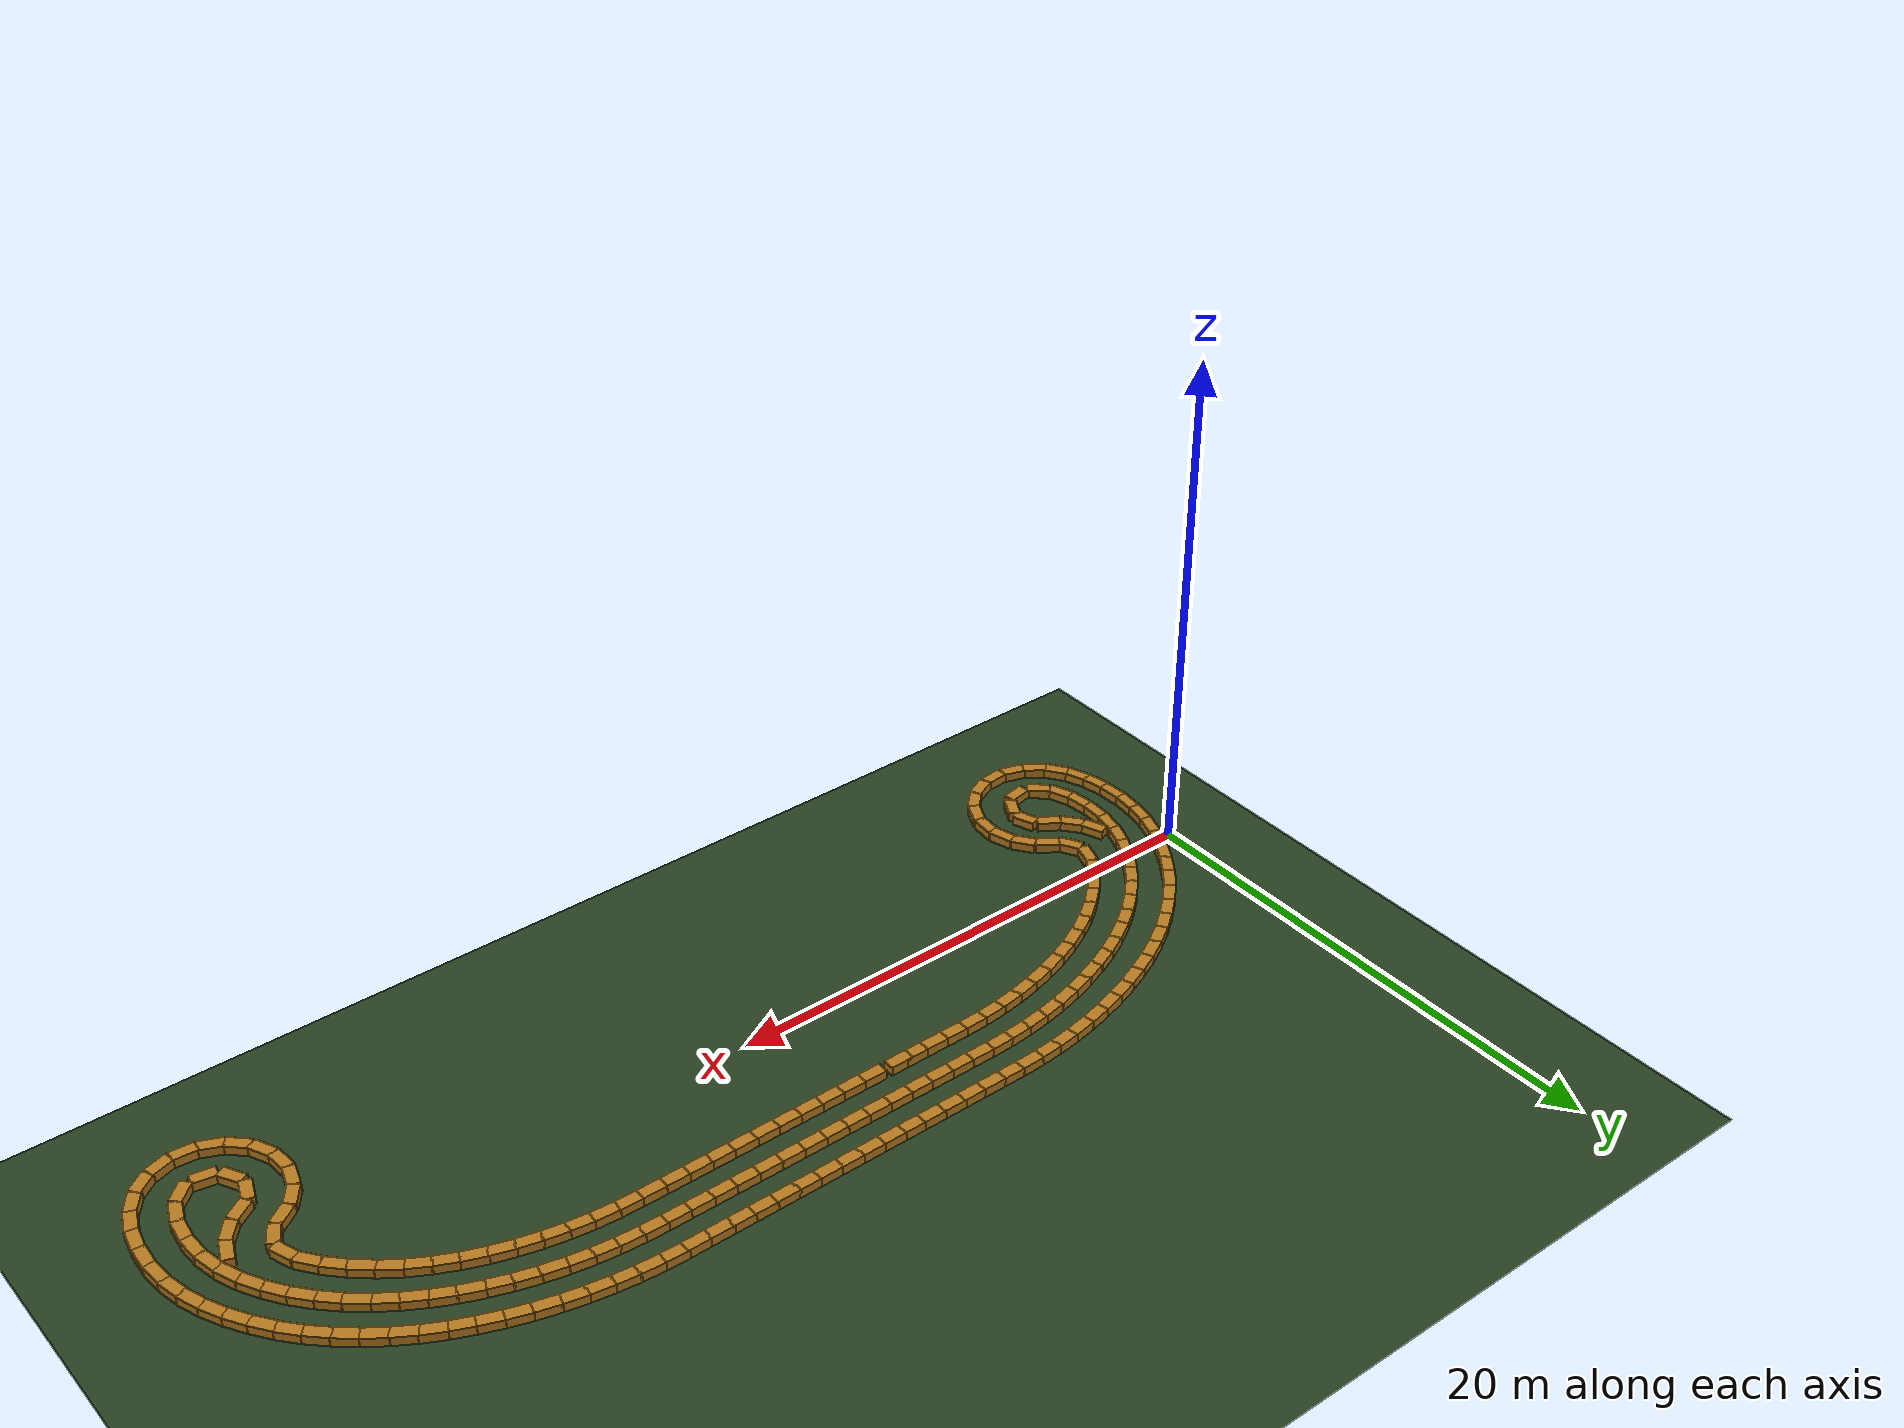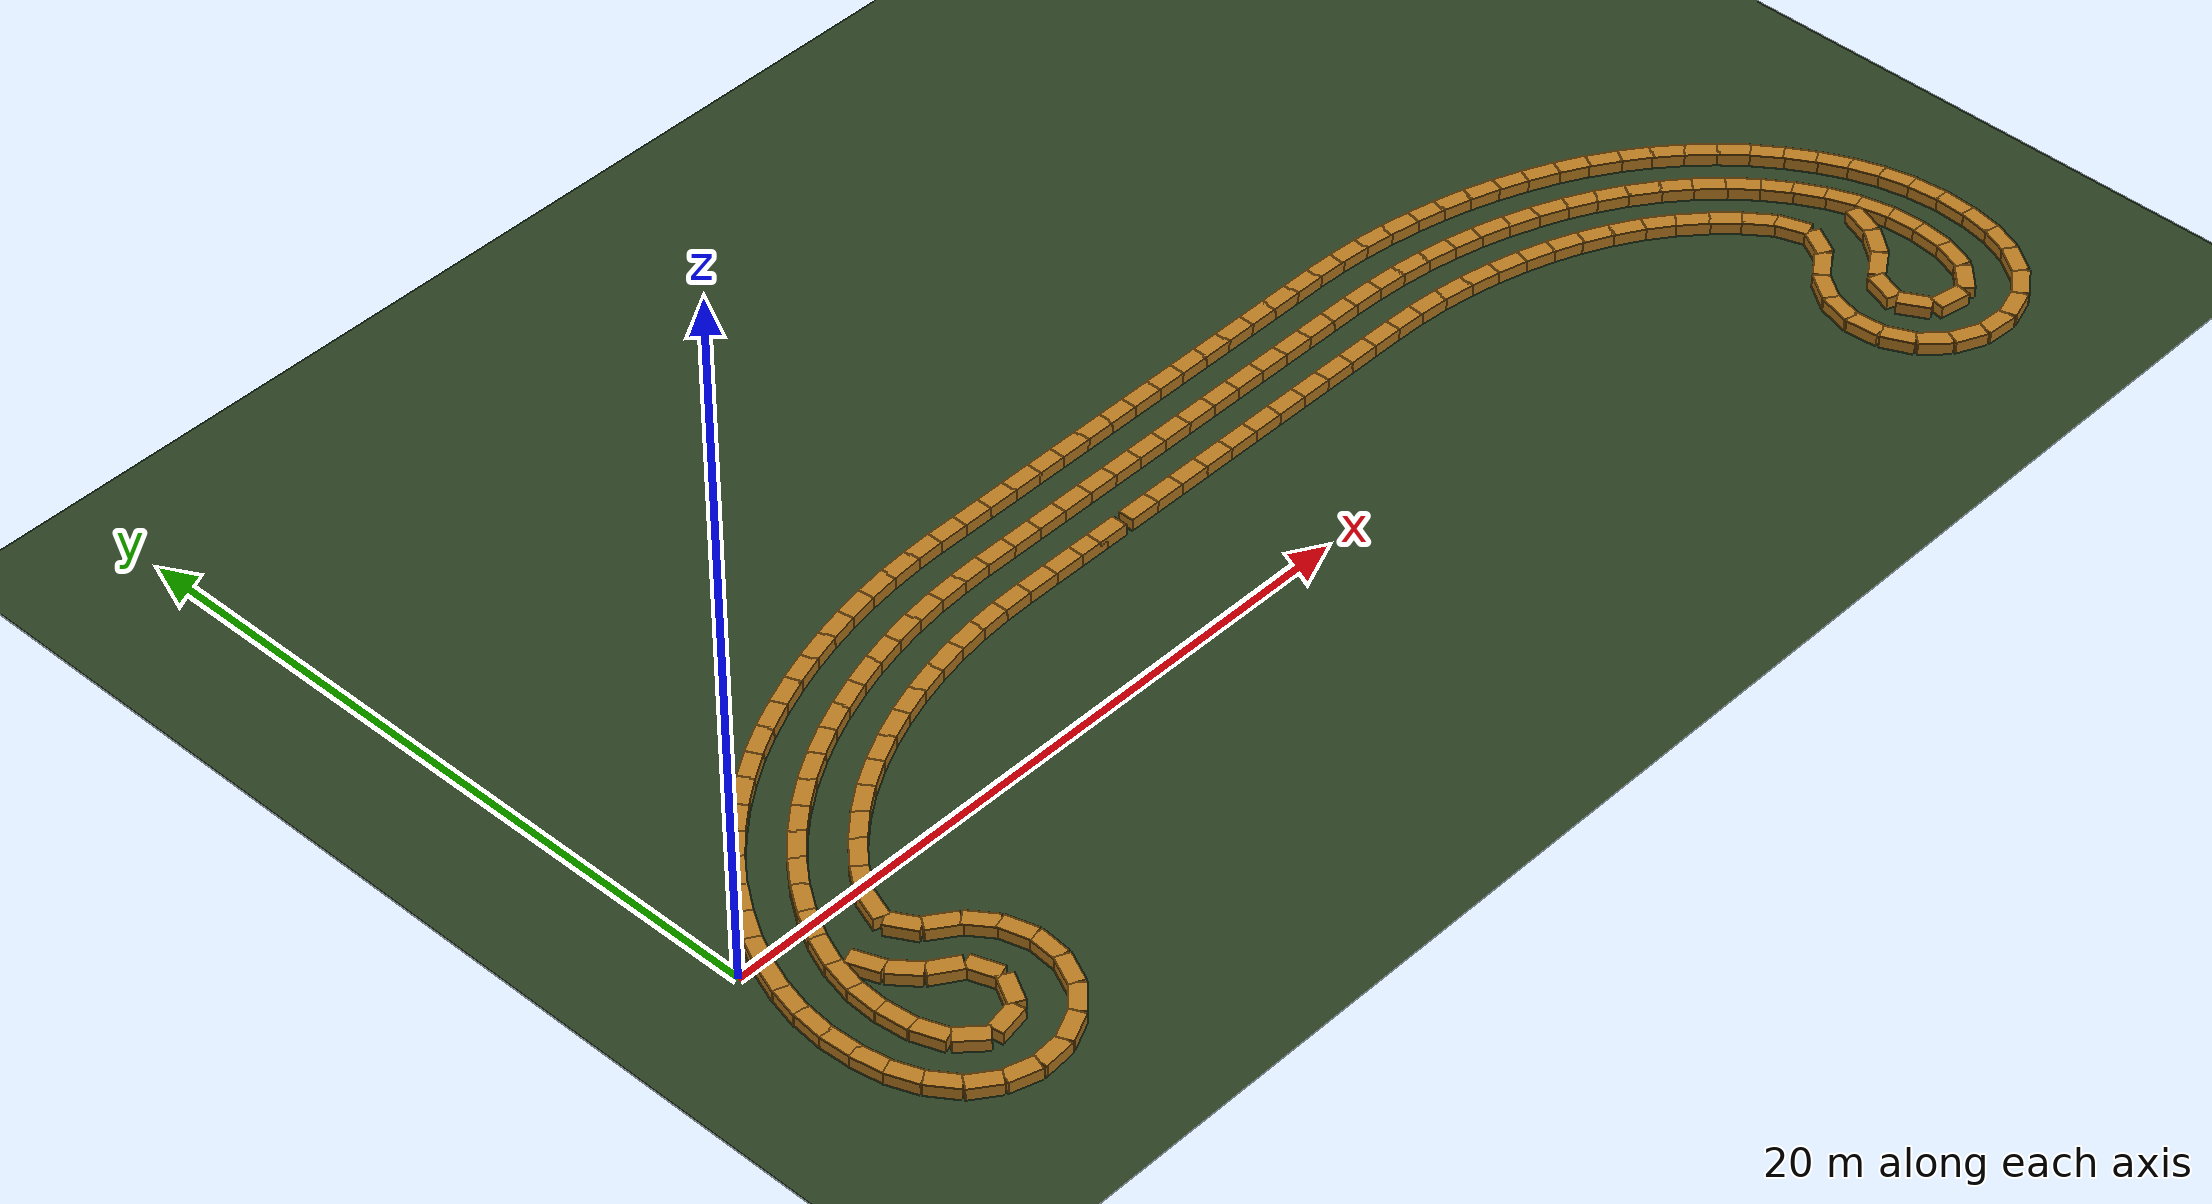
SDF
<sdf version="1.10">
 <world name="cfr_speed_course">
  <physics name="1ms" type="ignored">
   <max_step_size>0.001</max_step_size>
   <real_time_factor>1.0</real_time_factor>
  </physics>
  <plugin filename="gz-sim-physics-system" name="gz::sim::systems::Physics"/>
  <plugin filename="gz-sim-user-commands-system" name="gz::sim::systems::UserCommands"/>
  <plugin filename="gz-sim-scene-broadcaster-system" name="gz::sim::systems::SceneBroadcaster"/>
  <plugin filename="gz-sim-contact-system" name="gz::sim::systems::Contact"/>
  <plugin filename="gz-sim-imu-system" name="gz::sim::systems::Imu"/>
  <plugin filename="gz-sim-sensors-system" name="gz::sim::systems::Sensors">
   <render_engine>ogre2</render_engine>
  </plugin>
  <light type="directional" name="sun">
   <pose>0 0 20 0 0 0</pose>
   <diffuse>0.8 0.8 0.8 1</diffuse>
   <specular>0.2 0.2 0.2 1</specular>
   <direction>-0.4 0.2 -0.9</direction>
  </light>
  <model name="ground">
   <static>true</static>
   <pose>20.5 0 0 0 0 0</pose>
   <link name="link">
    <collision name="collision">
     <geometry><plane><normal>0 0 1</normal><size>60 45</size></plane></geometry>
     <surface>
      <friction>
       <ode><mu>50</mu></ode>
       <bullet><friction>1</friction><rolling_friction>0.001</rolling_friction></bullet>
      </friction>
     </surface>
    </collision>
    <visual name="visual">
     <geometry><plane><normal>0 0 1</normal><size>60 45</size></plane></geometry>
     <material><diffuse>0.16 0.25 0.13 1</diffuse></material>
    </visual>
   </link>
  </model>
  <model name="course_bales">
   <static>true</static>
   <link name="bales">
    <collision name="bale_0_collision">
     <pose>26.6032 4.0673 0.1778 0 0 0.00000</pose>
     <geometry><box><size>0.9144 0.4572 0.3556</size></box></geometry>
     <surface>
      <friction>
       <ode><mu>50</mu><mu2>50</mu2></ode>
       <bullet><friction>50</friction><friction2>50</friction2></bullet>
      </friction>
     </surface>
    </collision>
    <visual name="bale_0_visual">
     <pose>26.6032 4.0673 0.1778 0 0 0.00000</pose>
     <geometry><box><size>0.9144 0.4572 0.3556</size></box></geometry>
     <material><diffuse>0.72 0.48 0.12 1</diffuse><specular>0.08 0.05 0.01 1</specular></material>
    </visual>
    <collision name="bale_1_collision">
     <pose>27.4748 4.0566 0.1778 0 0 -0.02481</pose>
     <geometry><box><size>0.9144 0.4572 0.3556</size></box></geometry>
     <surface>
      <friction>
       <ode><mu>50</mu><mu2>50</mu2></ode>
       <bullet><friction>50</friction><friction2>50</friction2></bullet>
      </friction>
     </surface>
    </collision>
    <visual name="bale_1_visual">
     <pose>27.4748 4.0566 0.1778 0 0 -0.02481</pose>
     <geometry><box><size>0.9144 0.4572 0.3556</size></box></geometry>
     <material><diffuse>0.72 0.48 0.12 1</diffuse><specular>0.08 0.05 0.01 1</specular></material>
    </visual>
    <collision name="bale_2_collision">
     <pose>28.3503 4.0119 0.1778 0 0 -0.07955</pose>
     <geometry><box><size>0.9144 0.4572 0.3556</size></box></geometry>
     <surface>
      <friction>
       <ode><mu>50</mu><mu2>50</mu2></ode>
       <bullet><friction>50</friction><friction2>50</friction2></bullet>
      </friction>
     </surface>
    </collision>
    <visual name="bale_2_visual">
     <pose>28.3503 4.0119 0.1778 0 0 -0.07955</pose>
     <geometry><box><size>0.9144 0.4572 0.3556</size></box></geometry>
     <material><diffuse>0.72 0.48 0.12 1</diffuse><specular>0.08 0.05 0.01 1</specular></material>
    </visual>
    <collision name="bale_3_collision">
     <pose>29.2159 3.9170 0.1778 0 0 -0.13797</pose>
     <geometry><box><size>0.9144 0.4572 0.3556</size></box></geometry>
     <surface>
      <friction>
       <ode><mu>50</mu><mu2>50</mu2></ode>
       <bullet><friction>50</friction><friction2>50</friction2></bullet>
      </friction>
     </surface>
    </collision>
    <visual name="bale_3_visual">
     <pose>29.2159 3.9170 0.1778 0 0 -0.13797</pose>
     <geometry><box><size>0.9144 0.4572 0.3556</size></box></geometry>
     <material><diffuse>0.72 0.48 0.12 1</diffuse><specular>0.08 0.05 0.01 1</specular></material>
    </visual>
    <collision name="bale_4_collision">
     <pose>30.0712 3.7752 0.1778 0 0 -0.19542</pose>
     <geometry><box><size>0.9144 0.4572 0.3556</size></box></geometry>
     <surface>
      <friction>
       <ode><mu>50</mu><mu2>50</mu2></ode>
       <bullet><friction>50</friction><friction2>50</friction2></bullet>
      </friction>
     </surface>
    </collision>
    <visual name="bale_4_visual">
     <pose>30.0712 3.7752 0.1778 0 0 -0.19542</pose>
     <geometry><box><size>0.9144 0.4572 0.3556</size></box></geometry>
     <material><diffuse>0.72 0.48 0.12 1</diffuse><specular>0.08 0.05 0.01 1</specular></material>
    </visual>
    <collision name="bale_5_collision">
     <pose>30.9182 3.5816 0.1778 0 0 -0.25552</pose>
     <geometry><box><size>0.9144 0.4572 0.3556</size></box></geometry>
     <surface>
      <friction>
       <ode><mu>50</mu><mu2>50</mu2></ode>
       <bullet><friction>50</friction><friction2>50</friction2></bullet>
      </friction>
     </surface>
    </collision>
    <visual name="bale_5_visual">
     <pose>30.9182 3.5816 0.1778 0 0 -0.25552</pose>
     <geometry><box><size>0.9144 0.4572 0.3556</size></box></geometry>
     <material><diffuse>0.72 0.48 0.12 1</diffuse><specular>0.08 0.05 0.01 1</specular></material>
    </visual>
    <collision name="bale_6_collision">
     <pose>31.7486 3.3398 0.1778 0 0 -0.31765</pose>
     <geometry><box><size>0.9144 0.4572 0.3556</size></box></geometry>
     <surface>
      <friction>
       <ode><mu>50</mu><mu2>50</mu2></ode>
       <bullet><friction>50</friction><friction2>50</friction2></bullet>
      </friction>
     </surface>
    </collision>
    <visual name="bale_6_visual">
     <pose>31.7486 3.3398 0.1778 0 0 -0.31765</pose>
     <geometry><box><size>0.9144 0.4572 0.3556</size></box></geometry>
     <material><diffuse>0.72 0.48 0.12 1</diffuse><specular>0.08 0.05 0.01 1</specular></material>
    </visual>
    <collision name="bale_7_collision">
     <pose>32.5635 3.0449 0.1778 0 0 -0.38051</pose>
     <geometry><box><size>0.9144 0.4572 0.3556</size></box></geometry>
     <surface>
      <friction>
       <ode><mu>50</mu><mu2>50</mu2></ode>
       <bullet><friction>50</friction><friction2>50</friction2></bullet>
      </friction>
     </surface>
    </collision>
    <visual name="bale_7_visual">
     <pose>32.5635 3.0449 0.1778 0 0 -0.38051</pose>
     <geometry><box><size>0.9144 0.4572 0.3556</size></box></geometry>
     <material><diffuse>0.72 0.48 0.12 1</diffuse><specular>0.08 0.05 0.01 1</specular></material>
    </visual>
    <collision name="bale_8_collision">
     <pose>33.3534 2.6903 0.1778 0 0 -0.45239</pose>
     <geometry><box><size>0.9144 0.4572 0.3556</size></box></geometry>
     <surface>
      <friction>
       <ode><mu>50</mu><mu2>50</mu2></ode>
       <bullet><friction>50</friction><friction2>50</friction2></bullet>
      </friction>
     </surface>
    </collision>
    <visual name="bale_8_visual">
     <pose>33.3534 2.6903 0.1778 0 0 -0.45239</pose>
     <geometry><box><size>0.9144 0.4572 0.3556</size></box></geometry>
     <material><diffuse>0.72 0.48 0.12 1</diffuse><specular>0.08 0.05 0.01 1</specular></material>
    </visual>
    <collision name="bale_9_collision">
     <pose>34.1161 2.2829 0.1778 0 0 -0.52957</pose>
     <geometry><box><size>0.9144 0.4572 0.3556</size></box></geometry>
     <surface>
      <friction>
       <ode><mu>50</mu><mu2>50</mu2></ode>
       <bullet><friction>50</friction><friction2>50</friction2></bullet>
      </friction>
     </surface>
    </collision>
    <visual name="bale_9_visual">
     <pose>34.1161 2.2829 0.1778 0 0 -0.52957</pose>
     <geometry><box><size>0.9144 0.4572 0.3556</size></box></geometry>
     <material><diffuse>0.72 0.48 0.12 1</diffuse><specular>0.08 0.05 0.01 1</specular></material>
    </visual>
    <collision name="bale_10_collision">
     <pose>34.8450 1.8127 0.1778 0 0 -0.62427</pose>
     <geometry><box><size>0.9144 0.4572 0.3556</size></box></geometry>
     <surface>
      <friction>
       <ode><mu>50</mu><mu2>50</mu2></ode>
       <bullet><friction>50</friction><friction2>50</friction2></bullet>
      </friction>
     </surface>
    </collision>
    <visual name="bale_10_visual">
     <pose>34.8450 1.8127 0.1778 0 0 -0.62427</pose>
     <geometry><box><size>0.9144 0.4572 0.3556</size></box></geometry>
     <material><diffuse>0.72 0.48 0.12 1</diffuse><specular>0.08 0.05 0.01 1</specular></material>
    </visual>
    <collision name="bale_11_collision">
     <pose>35.5260 1.2686 0.1778 0 0 -0.71379</pose>
     <geometry><box><size>0.9144 0.4572 0.3556</size></box></geometry>
     <surface>
      <friction>
       <ode><mu>50</mu><mu2>50</mu2></ode>
       <bullet><friction>50</friction><friction2>50</friction2></bullet>
      </friction>
     </surface>
    </collision>
    <visual name="bale_11_visual">
     <pose>35.5260 1.2686 0.1778 0 0 -0.71379</pose>
     <geometry><box><size>0.9144 0.4572 0.3556</size></box></geometry>
     <material><diffuse>0.72 0.48 0.12 1</diffuse><specular>0.08 0.05 0.01 1</specular></material>
    </visual>
    <collision name="bale_12_collision">
     <pose>36.1545 0.6706 0.1778 0 0 -0.81133</pose>
     <geometry><box><size>0.9144 0.4572 0.3556</size></box></geometry>
     <surface>
      <friction>
       <ode><mu>50</mu><mu2>50</mu2></ode>
       <bullet><friction>50</friction><friction2>50</friction2></bullet>
      </friction>
     </surface>
    </collision>
    <visual name="bale_12_visual">
     <pose>36.1545 0.6706 0.1778 0 0 -0.81133</pose>
     <geometry><box><size>0.9144 0.4572 0.3556</size></box></geometry>
     <material><diffuse>0.72 0.48 0.12 1</diffuse><specular>0.08 0.05 0.01 1</specular></material>
    </visual>
    <collision name="bale_13_collision">
     <pose>36.7101 0.0093 0.1778 0 0 -0.92389</pose>
     <geometry><box><size>0.9144 0.4572 0.3556</size></box></geometry>
     <surface>
      <friction>
       <ode><mu>50</mu><mu2>50</mu2></ode>
       <bullet><friction>50</friction><friction2>50</friction2></bullet>
      </friction>
     </surface>
    </collision>
    <visual name="bale_13_visual">
     <pose>36.7101 0.0093 0.1778 0 0 -0.92389</pose>
     <geometry><box><size>0.9144 0.4572 0.3556</size></box></geometry>
     <material><diffuse>0.72 0.48 0.12 1</diffuse><specular>0.08 0.05 0.01 1</specular></material>
    </visual>
    <collision name="bale_14_collision">
     <pose>37.1231 -0.7633 0.1778 0 0 -1.23370</pose>
     <geometry><box><size>0.9144 0.4572 0.3556</size></box></geometry>
     <surface>
      <friction>
       <ode><mu>50</mu><mu2>50</mu2></ode>
       <bullet><friction>50</friction><friction2>50</friction2></bullet>
      </friction>
     </surface>
    </collision>
    <visual name="bale_14_visual">
     <pose>37.1231 -0.7633 0.1778 0 0 -1.23370</pose>
     <geometry><box><size>0.9144 0.4572 0.3556</size></box></geometry>
     <material><diffuse>0.72 0.48 0.12 1</diffuse><specular>0.08 0.05 0.01 1</specular></material>
    </visual>
    <collision name="bale_15_collision">
     <pose>37.0435 -1.6473 0.1778 0 0 -2.09001</pose>
     <geometry><box><size>0.9144 0.4572 0.3556</size></box></geometry>
     <surface>
      <friction>
       <ode><mu>50</mu><mu2>50</mu2></ode>
       <bullet><friction>50</friction><friction2>50</friction2></bullet>
      </friction>
     </surface>
    </collision>
    <visual name="bale_15_visual">
     <pose>37.0435 -1.6473 0.1778 0 0 -2.09001</pose>
     <geometry><box><size>0.9144 0.4572 0.3556</size></box></geometry>
     <material><diffuse>0.72 0.48 0.12 1</diffuse><specular>0.08 0.05 0.01 1</specular></material>
    </visual>
    <collision name="bale_16_collision">
     <pose>36.4189 -2.2734 0.1778 0 0 -2.53115</pose>
     <geometry><box><size>0.9144 0.4572 0.3556</size></box></geometry>
     <surface>
      <friction>
       <ode><mu>50</mu><mu2>50</mu2></ode>
       <bullet><friction>50</friction><friction2>50</friction2></bullet>
      </friction>
     </surface>
    </collision>
    <visual name="bale_16_visual">
     <pose>36.4189 -2.2734 0.1778 0 0 -2.53115</pose>
     <geometry><box><size>0.9144 0.4572 0.3556</size></box></geometry>
     <material><diffuse>0.72 0.48 0.12 1</diffuse><specular>0.08 0.05 0.01 1</specular></material>
    </visual>
    <collision name="bale_17_collision">
     <pose>35.7735 -2.8872 0.1778 0 0 -2.19741</pose>
     <geometry><box><size>0.9144 0.4572 0.3556</size></box></geometry>
     <surface>
      <friction>
       <ode><mu>50</mu><mu2>50</mu2></ode>
       <bullet><friction>50</friction><friction2>50</friction2></bullet>
      </friction>
     </surface>
    </collision>
    <visual name="bale_17_visual">
     <pose>35.7735 -2.8872 0.1778 0 0 -2.19741</pose>
     <geometry><box><size>0.9144 0.4572 0.3556</size></box></geometry>
     <material><diffuse>0.72 0.48 0.12 1</diffuse><specular>0.08 0.05 0.01 1</specular></material>
    </visual>
    <collision name="bale_18_collision">
     <pose>35.3884 -3.6816 0.1778 0 0 -1.85005</pose>
     <geometry><box><size>0.9144 0.4572 0.3556</size></box></geometry>
     <surface>
      <friction>
       <ode><mu>50</mu><mu2>50</mu2></ode>
       <bullet><friction>50</friction><friction2>50</friction2></bullet>
      </friction>
     </surface>
    </collision>
    <visual name="bale_18_visual">
     <pose>35.3884 -3.6816 0.1778 0 0 -1.85005</pose>
     <geometry><box><size>0.9144 0.4572 0.3556</size></box></geometry>
     <material><diffuse>0.72 0.48 0.12 1</diffuse><specular>0.08 0.05 0.01 1</specular></material>
    </visual>
    <collision name="bale_19_collision">
     <pose>35.3013 -4.5573 0.1778 0 0 -1.48591</pose>
     <geometry><box><size>0.9144 0.4572 0.3556</size></box></geometry>
     <surface>
      <friction>
       <ode><mu>50</mu><mu2>50</mu2></ode>
       <bullet><friction>50</friction><friction2>50</friction2></bullet>
      </friction>
     </surface>
    </collision>
    <visual name="bale_19_visual">
     <pose>35.3013 -4.5573 0.1778 0 0 -1.48591</pose>
     <geometry><box><size>0.9144 0.4572 0.3556</size></box></geometry>
     <material><diffuse>0.72 0.48 0.12 1</diffuse><specular>0.08 0.05 0.01 1</specular></material>
    </visual>
    <collision name="bale_20_collision">
     <pose>35.5282 -5.4186 0.1778 0 0 -1.13446</pose>
     <geometry><box><size>0.9144 0.4572 0.3556</size></box></geometry>
     <surface>
      <friction>
       <ode><mu>50</mu><mu2>50</mu2></ode>
       <bullet><friction>50</friction><friction2>50</friction2></bullet>
      </friction>
     </surface>
    </collision>
    <visual name="bale_20_visual">
     <pose>35.5282 -5.4186 0.1778 0 0 -1.13446</pose>
     <geometry><box><size>0.9144 0.4572 0.3556</size></box></geometry>
     <material><diffuse>0.72 0.48 0.12 1</diffuse><specular>0.08 0.05 0.01 1</specular></material>
    </visual>
    <collision name="bale_21_collision">
     <pose>36.0402 -6.1499 0.1778 0 0 -0.76672</pose>
     <geometry><box><size>0.9144 0.4572 0.3556</size></box></geometry>
     <surface>
      <friction>
       <ode><mu>50</mu><mu2>50</mu2></ode>
       <bullet><friction>50</friction><friction2>50</friction2></bullet>
      </friction>
     </surface>
    </collision>
    <visual name="bale_21_visual">
     <pose>36.0402 -6.1499 0.1778 0 0 -0.76672</pose>
     <geometry><box><size>0.9144 0.4572 0.3556</size></box></geometry>
     <material><diffuse>0.72 0.48 0.12 1</diffuse><specular>0.08 0.05 0.01 1</specular></material>
    </visual>
    <collision name="bale_22_collision">
     <pose>36.7716 -6.6517 0.1778 0 0 -0.42909</pose>
     <geometry><box><size>0.9144 0.4572 0.3556</size></box></geometry>
     <surface>
      <friction>
       <ode><mu>50</mu><mu2>50</mu2></ode>
       <bullet><friction>50</friction><friction2>50</friction2></bullet>
      </friction>
     </surface>
    </collision>
    <visual name="bale_22_visual">
     <pose>36.7716 -6.6517 0.1778 0 0 -0.42909</pose>
     <geometry><box><size>0.9144 0.4572 0.3556</size></box></geometry>
     <material><diffuse>0.72 0.48 0.12 1</diffuse><specular>0.08 0.05 0.01 1</specular></material>
    </visual>
    <collision name="bale_23_collision">
     <pose>37.6277 -6.8740 0.1778 0 0 -0.07325</pose>
     <geometry><box><size>0.9144 0.4572 0.3556</size></box></geometry>
     <surface>
      <friction>
       <ode><mu>50</mu><mu2>50</mu2></ode>
       <bullet><friction>50</friction><friction2>50</friction2></bullet>
      </friction>
     </surface>
    </collision>
    <visual name="bale_23_visual">
     <pose>37.6277 -6.8740 0.1778 0 0 -0.07325</pose>
     <geometry><box><size>0.9144 0.4572 0.3556</size></box></geometry>
     <material><diffuse>0.72 0.48 0.12 1</diffuse><specular>0.08 0.05 0.01 1</specular></material>
    </visual>
    <collision name="bale_24_collision">
     <pose>38.5174 -6.7757 0.1778 0 0 0.30111</pose>
     <geometry><box><size>0.9144 0.4572 0.3556</size></box></geometry>
     <surface>
      <friction>
       <ode><mu>50</mu><mu2>50</mu2></ode>
       <bullet><friction>50</friction><friction2>50</friction2></bullet>
      </friction>
     </surface>
    </collision>
    <visual name="bale_24_visual">
     <pose>38.5174 -6.7757 0.1778 0 0 0.30111</pose>
     <geometry><box><size>0.9144 0.4572 0.3556</size></box></geometry>
     <material><diffuse>0.72 0.48 0.12 1</diffuse><specular>0.08 0.05 0.01 1</specular></material>
    </visual>
    <collision name="bale_25_collision">
     <pose>39.3181 -6.3785 0.1778 0 0 0.62483</pose>
     <geometry><box><size>0.9144 0.4572 0.3556</size></box></geometry>
     <surface>
      <friction>
       <ode><mu>50</mu><mu2>50</mu2></ode>
       <bullet><friction>50</friction><friction2>50</friction2></bullet>
      </friction>
     </surface>
    </collision>
    <visual name="bale_25_visual">
     <pose>39.3181 -6.3785 0.1778 0 0 0.62483</pose>
     <geometry><box><size>0.9144 0.4572 0.3556</size></box></geometry>
     <material><diffuse>0.72 0.48 0.12 1</diffuse><specular>0.08 0.05 0.01 1</specular></material>
    </visual>
    <collision name="bale_26_collision">
     <pose>39.9295 -5.7330 0.1778 0 0 0.95993</pose>
     <geometry><box><size>0.9144 0.4572 0.3556</size></box></geometry>
     <surface>
      <friction>
       <ode><mu>50</mu><mu2>50</mu2></ode>
       <bullet><friction>50</friction><friction2>50</friction2></bullet>
      </friction>
     </surface>
    </collision>
    <visual name="bale_26_visual">
     <pose>39.9295 -5.7330 0.1778 0 0 0.95993</pose>
     <geometry><box><size>0.9144 0.4572 0.3556</size></box></geometry>
     <material><diffuse>0.72 0.48 0.12 1</diffuse><specular>0.08 0.05 0.01 1</specular></material>
    </visual>
    <collision name="bale_27_collision">
     <pose>40.3455 -4.9548 0.1778 0 0 1.20065</pose>
     <geometry><box><size>0.9144 0.4572 0.3556</size></box></geometry>
     <surface>
      <friction>
       <ode><mu>50</mu><mu2>50</mu2></ode>
       <bullet><friction>50</friction><friction2>50</friction2></bullet>
      </friction>
     </surface>
    </collision>
    <visual name="bale_27_visual">
     <pose>40.3455 -4.9548 0.1778 0 0 1.20065</pose>
     <geometry><box><size>0.9144 0.4572 0.3556</size></box></geometry>
     <material><diffuse>0.72 0.48 0.12 1</diffuse><specular>0.08 0.05 0.01 1</specular></material>
    </visual>
    <collision name="bale_28_collision">
     <pose>40.5751 -4.1179 0.1778 0 0 1.38666</pose>
     <geometry><box><size>0.9144 0.4572 0.3556</size></box></geometry>
     <surface>
      <friction>
       <ode><mu>50</mu><mu2>50</mu2></ode>
       <bullet><friction>50</friction><friction2>50</friction2></bullet>
      </friction>
     </surface>
    </collision>
    <visual name="bale_28_visual">
     <pose>40.5751 -4.1179 0.1778 0 0 1.38666</pose>
     <geometry><box><size>0.9144 0.4572 0.3556</size></box></geometry>
     <material><diffuse>0.72 0.48 0.12 1</diffuse><specular>0.08 0.05 0.01 1</specular></material>
    </visual>
    <collision name="bale_29_collision">
     <pose>40.6654 -3.2533 0.1778 0 0 1.51669</pose>
     <geometry><box><size>0.9144 0.4572 0.3556</size></box></geometry>
     <surface>
      <friction>
       <ode><mu>50</mu><mu2>50</mu2></ode>
       <bullet><friction>50</friction><friction2>50</friction2></bullet>
      </friction>
     </surface>
    </collision>
    <visual name="bale_29_visual">
     <pose>40.6654 -3.2533 0.1778 0 0 1.51669</pose>
     <geometry><box><size>0.9144 0.4572 0.3556</size></box></geometry>
     <material><diffuse>0.72 0.48 0.12 1</diffuse><specular>0.08 0.05 0.01 1</specular></material>
    </visual>
    <collision name="bale_30_collision">
     <pose>40.6451 -2.3866 0.1778 0 0 -4.60915</pose>
     <geometry><box><size>0.9144 0.4572 0.3556</size></box></geometry>
     <surface>
      <friction>
       <ode><mu>50</mu><mu2>50</mu2></ode>
       <bullet><friction>50</friction><friction2>50</friction2></bullet>
      </friction>
     </surface>
    </collision>
    <visual name="bale_30_visual">
     <pose>40.6451 -2.3866 0.1778 0 0 -4.60915</pose>
     <geometry><box><size>0.9144 0.4572 0.3556</size></box></geometry>
     <material><diffuse>0.72 0.48 0.12 1</diffuse><specular>0.08 0.05 0.01 1</specular></material>
    </visual>
    <collision name="bale_31_collision">
     <pose>40.5157 -1.5271 0.1778 0 0 -4.47812</pose>
     <geometry><box><size>0.9144 0.4572 0.3556</size></box></geometry>
     <surface>
      <friction>
       <ode><mu>50</mu><mu2>50</mu2></ode>
       <bullet><friction>50</friction><friction2>50</friction2></bullet>
      </friction>
     </surface>
    </collision>
    <visual name="bale_31_visual">
     <pose>40.5157 -1.5271 0.1778 0 0 -4.47812</pose>
     <geometry><box><size>0.9144 0.4572 0.3556</size></box></geometry>
     <material><diffuse>0.72 0.48 0.12 1</diffuse><specular>0.08 0.05 0.01 1</specular></material>
    </visual>
    <collision name="bale_32_collision">
     <pose>40.2756 -0.6903 0.1778 0 0 -4.36301</pose>
     <geometry><box><size>0.9144 0.4572 0.3556</size></box></geometry>
     <surface>
      <friction>
       <ode><mu>50</mu><mu2>50</mu2></ode>
       <bullet><friction>50</friction><friction2>50</friction2></bullet>
      </friction>
     </surface>
    </collision>
    <visual name="bale_32_visual">
     <pose>40.2756 -0.6903 0.1778 0 0 -4.36301</pose>
     <geometry><box><size>0.9144 0.4572 0.3556</size></box></geometry>
     <material><diffuse>0.72 0.48 0.12 1</diffuse><specular>0.08 0.05 0.01 1</specular></material>
    </visual>
    <collision name="bale_33_collision">
     <pose>39.9386 0.1112 0.1778 0 0 -4.26047</pose>
     <geometry><box><size>0.9144 0.4572 0.3556</size></box></geometry>
     <surface>
      <friction>
       <ode><mu>50</mu><mu2>50</mu2></ode>
       <bullet><friction>50</friction><friction2>50</friction2></bullet>
      </friction>
     </surface>
    </collision>
    <visual name="bale_33_visual">
     <pose>39.9386 0.1112 0.1778 0 0 -4.26047</pose>
     <geometry><box><size>0.9144 0.4572 0.3556</size></box></geometry>
     <material><diffuse>0.72 0.48 0.12 1</diffuse><specular>0.08 0.05 0.01 1</specular></material>
    </visual>
    <collision name="bale_34_collision">
     <pose>39.5202 0.8720 0.1778 0 0 -4.16749</pose>
     <geometry><box><size>0.9144 0.4572 0.3556</size></box></geometry>
     <surface>
      <friction>
       <ode><mu>50</mu><mu2>50</mu2></ode>
       <bullet><friction>50</friction><friction2>50</friction2></bullet>
      </friction>
     </surface>
    </collision>
    <visual name="bale_34_visual">
     <pose>39.5202 0.8720 0.1778 0 0 -4.16749</pose>
     <geometry><box><size>0.9144 0.4572 0.3556</size></box></geometry>
     <material><diffuse>0.72 0.48 0.12 1</diffuse><specular>0.08 0.05 0.01 1</specular></material>
    </visual>
    <collision name="bale_35_collision">
     <pose>39.0374 1.5971 0.1778 0 0 -4.08621</pose>
     <geometry><box><size>0.9144 0.4572 0.3556</size></box></geometry>
     <surface>
      <friction>
       <ode><mu>50</mu><mu2>50</mu2></ode>
       <bullet><friction>50</friction><friction2>50</friction2></bullet>
      </friction>
     </surface>
    </collision>
    <visual name="bale_35_visual">
     <pose>39.0374 1.5971 0.1778 0 0 -4.08621</pose>
     <geometry><box><size>0.9144 0.4572 0.3556</size></box></geometry>
     <material><diffuse>0.72 0.48 0.12 1</diffuse><specular>0.08 0.05 0.01 1</specular></material>
    </visual>
    <collision name="bale_36_collision">
     <pose>38.5012 2.2838 0.1778 0 0 -3.99252</pose>
     <geometry><box><size>0.9144 0.4572 0.3556</size></box></geometry>
     <surface>
      <friction>
       <ode><mu>50</mu><mu2>50</mu2></ode>
       <bullet><friction>50</friction><friction2>50</friction2></bullet>
      </friction>
     </surface>
    </collision>
    <visual name="bale_36_visual">
     <pose>38.5012 2.2838 0.1778 0 0 -3.99252</pose>
     <geometry><box><size>0.9144 0.4572 0.3556</size></box></geometry>
     <material><diffuse>0.72 0.48 0.12 1</diffuse><specular>0.08 0.05 0.01 1</specular></material>
    </visual>
    <collision name="bale_37_collision">
     <pose>37.9063 2.9127 0.1778 0 0 -3.91149</pose>
     <geometry><box><size>0.9144 0.4572 0.3556</size></box></geometry>
     <surface>
      <friction>
       <ode><mu>50</mu><mu2>50</mu2></ode>
       <bullet><friction>50</friction><friction2>50</friction2></bullet>
      </friction>
     </surface>
    </collision>
    <visual name="bale_37_visual">
     <pose>37.9063 2.9127 0.1778 0 0 -3.91149</pose>
     <geometry><box><size>0.9144 0.4572 0.3556</size></box></geometry>
     <material><diffuse>0.72 0.48 0.12 1</diffuse><specular>0.08 0.05 0.01 1</specular></material>
    </visual>
    <collision name="bale_38_collision">
     <pose>37.2643 3.4976 0.1778 0 0 -3.83972</pose>
     <geometry><box><size>0.9144 0.4572 0.3556</size></box></geometry>
     <surface>
      <friction>
       <ode><mu>50</mu><mu2>50</mu2></ode>
       <bullet><friction>50</friction><friction2>50</friction2></bullet>
      </friction>
     </surface>
    </collision>
    <visual name="bale_38_visual">
     <pose>37.2643 3.4976 0.1778 0 0 -3.83972</pose>
     <geometry><box><size>0.9144 0.4572 0.3556</size></box></geometry>
     <material><diffuse>0.72 0.48 0.12 1</diffuse><specular>0.08 0.05 0.01 1</specular></material>
    </visual>
    <collision name="bale_39_collision">
     <pose>36.5780 4.0389 0.1778 0 0 -3.76805</pose>
     <geometry><box><size>0.9144 0.4572 0.3556</size></box></geometry>
     <surface>
      <friction>
       <ode><mu>50</mu><mu2>50</mu2></ode>
       <bullet><friction>50</friction><friction2>50</friction2></bullet>
      </friction>
     </surface>
    </collision>
    <visual name="bale_39_visual">
     <pose>36.5780 4.0389 0.1778 0 0 -3.76805</pose>
     <geometry><box><size>0.9144 0.4572 0.3556</size></box></geometry>
     <material><diffuse>0.72 0.48 0.12 1</diffuse><specular>0.08 0.05 0.01 1</specular></material>
    </visual>
    <collision name="bale_40_collision">
     <pose>35.8578 4.5224 0.1778 0 0 -3.70314</pose>
     <geometry><box><size>0.9144 0.4572 0.3556</size></box></geometry>
     <surface>
      <friction>
       <ode><mu>50</mu><mu2>50</mu2></ode>
       <bullet><friction>50</friction><friction2>50</friction2></bullet>
      </friction>
     </surface>
    </collision>
    <visual name="bale_40_visual">
     <pose>35.8578 4.5224 0.1778 0 0 -3.70314</pose>
     <geometry><box><size>0.9144 0.4572 0.3556</size></box></geometry>
     <material><diffuse>0.72 0.48 0.12 1</diffuse><specular>0.08 0.05 0.01 1</specular></material>
    </visual>
    <collision name="bale_41_collision">
     <pose>35.1131 4.9604 0.1778 0 0 -3.63226</pose>
     <geometry><box><size>0.9144 0.4572 0.3556</size></box></geometry>
     <surface>
      <friction>
       <ode><mu>50</mu><mu2>50</mu2></ode>
       <bullet><friction>50</friction><friction2>50</friction2></bullet>
      </friction>
     </surface>
    </collision>
    <visual name="bale_41_visual">
     <pose>35.1131 4.9604 0.1778 0 0 -3.63226</pose>
     <geometry><box><size>0.9144 0.4572 0.3556</size></box></geometry>
     <material><diffuse>0.72 0.48 0.12 1</diffuse><specular>0.08 0.05 0.01 1</specular></material>
    </visual>
    <collision name="bale_42_collision">
     <pose>34.3333 5.3436 0.1778 0 0 -3.56718</pose>
     <geometry><box><size>0.9144 0.4572 0.3556</size></box></geometry>
     <surface>
      <friction>
       <ode><mu>50</mu><mu2>50</mu2></ode>
       <bullet><friction>50</friction><friction2>50</friction2></bullet>
      </friction>
     </surface>
    </collision>
    <visual name="bale_42_visual">
     <pose>34.3333 5.3436 0.1778 0 0 -3.56718</pose>
     <geometry><box><size>0.9144 0.4572 0.3556</size></box></geometry>
     <material><diffuse>0.72 0.48 0.12 1</diffuse><specular>0.08 0.05 0.01 1</specular></material>
    </visual>
    <collision name="bale_43_collision">
     <pose>33.5355 5.6822 0.1778 0 0 -3.51483</pose>
     <geometry><box><size>0.9144 0.4572 0.3556</size></box></geometry>
     <surface>
      <friction>
       <ode><mu>50</mu><mu2>50</mu2></ode>
       <bullet><friction>50</friction><friction2>50</friction2></bullet>
      </friction>
     </surface>
    </collision>
    <visual name="bale_43_visual">
     <pose>33.5355 5.6822 0.1778 0 0 -3.51483</pose>
     <geometry><box><size>0.9144 0.4572 0.3556</size></box></geometry>
     <material><diffuse>0.72 0.48 0.12 1</diffuse><specular>0.08 0.05 0.01 1</specular></material>
    </visual>
    <collision name="bale_44_collision">
     <pose>32.7204 5.9816 0.1778 0 0 -3.46082</pose>
     <geometry><box><size>0.9144 0.4572 0.3556</size></box></geometry>
     <surface>
      <friction>
       <ode><mu>50</mu><mu2>50</mu2></ode>
       <bullet><friction>50</friction><friction2>50</friction2></bullet>
      </friction>
     </surface>
    </collision>
    <visual name="bale_44_visual">
     <pose>32.7204 5.9816 0.1778 0 0 -3.46082</pose>
     <geometry><box><size>0.9144 0.4572 0.3556</size></box></geometry>
     <material><diffuse>0.72 0.48 0.12 1</diffuse><specular>0.08 0.05 0.01 1</specular></material>
    </visual>
    <collision name="bale_45_collision">
     <pose>31.8929 6.2340 0.1778 0 0 -3.41063</pose>
     <geometry><box><size>0.9144 0.4572 0.3556</size></box></geometry>
     <surface>
      <friction>
       <ode><mu>50</mu><mu2>50</mu2></ode>
       <bullet><friction>50</friction><friction2>50</friction2></bullet>
      </friction>
     </surface>
    </collision>
    <visual name="bale_45_visual">
     <pose>31.8929 6.2340 0.1778 0 0 -3.41063</pose>
     <geometry><box><size>0.9144 0.4572 0.3556</size></box></geometry>
     <material><diffuse>0.72 0.48 0.12 1</diffuse><specular>0.08 0.05 0.01 1</specular></material>
    </visual>
    <collision name="bale_46_collision">
     <pose>31.0572 6.4429 0.1778 0 0 -3.36420</pose>
     <geometry><box><size>0.9144 0.4572 0.3556</size></box></geometry>
     <surface>
      <friction>
       <ode><mu>50</mu><mu2>50</mu2></ode>
       <bullet><friction>50</friction><friction2>50</friction2></bullet>
      </friction>
     </surface>
    </collision>
    <visual name="bale_46_visual">
     <pose>31.0572 6.4429 0.1778 0 0 -3.36420</pose>
     <geometry><box><size>0.9144 0.4572 0.3556</size></box></geometry>
     <material><diffuse>0.72 0.48 0.12 1</diffuse><specular>0.08 0.05 0.01 1</specular></material>
    </visual>
    <collision name="bale_47_collision">
     <pose>30.2124 6.6073 0.1778 0 0 -3.31726</pose>
     <geometry><box><size>0.9144 0.4572 0.3556</size></box></geometry>
     <surface>
      <friction>
       <ode><mu>50</mu><mu2>50</mu2></ode>
       <bullet><friction>50</friction><friction2>50</friction2></bullet>
      </friction>
     </surface>
    </collision>
    <visual name="bale_47_visual">
     <pose>30.2124 6.6073 0.1778 0 0 -3.31726</pose>
     <geometry><box><size>0.9144 0.4572 0.3556</size></box></geometry>
     <material><diffuse>0.72 0.48 0.12 1</diffuse><specular>0.08 0.05 0.01 1</specular></material>
    </visual>
    <collision name="bale_48_collision">
     <pose>29.3622 6.7358 0.1778 0 0 -3.26734</pose>
     <geometry><box><size>0.9144 0.4572 0.3556</size></box></geometry>
     <surface>
      <friction>
       <ode><mu>50</mu><mu2>50</mu2></ode>
       <bullet><friction>50</friction><friction2>50</friction2></bullet>
      </friction>
     </surface>
    </collision>
    <visual name="bale_48_visual">
     <pose>29.3622 6.7358 0.1778 0 0 -3.26734</pose>
     <geometry><box><size>0.9144 0.4572 0.3556</size></box></geometry>
     <material><diffuse>0.72 0.48 0.12 1</diffuse><specular>0.08 0.05 0.01 1</specular></material>
    </visual>
    <collision name="bale_49_collision">
     <pose>28.5059 6.8216 0.1778 0 0 -3.21631</pose>
     <geometry><box><size>0.9144 0.4572 0.3556</size></box></geometry>
     <surface>
      <friction>
       <ode><mu>50</mu><mu2>50</mu2></ode>
       <bullet><friction>50</friction><friction2>50</friction2></bullet>
      </friction>
     </surface>
    </collision>
    <visual name="bale_49_visual">
     <pose>28.5059 6.8216 0.1778 0 0 -3.21631</pose>
     <geometry><box><size>0.9144 0.4572 0.3556</size></box></geometry>
     <material><diffuse>0.72 0.48 0.12 1</diffuse><specular>0.08 0.05 0.01 1</specular></material>
    </visual>
    <collision name="bale_50_collision">
     <pose>27.6488 6.8662 0.1778 0 0 -3.17465</pose>
     <geometry><box><size>0.9144 0.4572 0.3556</size></box></geometry>
     <surface>
      <friction>
       <ode><mu>50</mu><mu2>50</mu2></ode>
       <bullet><friction>50</friction><friction2>50</friction2></bullet>
      </friction>
     </surface>
    </collision>
    <visual name="bale_50_visual">
     <pose>27.6488 6.8662 0.1778 0 0 -3.17465</pose>
     <geometry><box><size>0.9144 0.4572 0.3556</size></box></geometry>
     <material><diffuse>0.72 0.48 0.12 1</diffuse><specular>0.08 0.05 0.01 1</specular></material>
    </visual>
    <collision name="bale_51_collision">
     <pose>25.7069 4.0673 0.1778 0 0 0.00000</pose>
     <geometry><box><size>0.9144 0.4572 0.3556</size></box></geometry>
     <surface>
      <friction>
       <ode><mu>50</mu><mu2>50</mu2></ode>
       <bullet><friction>50</friction><friction2>50</friction2></bullet>
      </friction>
     </surface>
    </collision>
    <visual name="bale_51_visual">
     <pose>25.7069 4.0673 0.1778 0 0 0.00000</pose>
     <geometry><box><size>0.9144 0.4572 0.3556</size></box></geometry>
     <material><diffuse>0.72 0.48 0.12 1</diffuse><specular>0.08 0.05 0.01 1</specular></material>
    </visual>
    <collision name="bale_52_collision">
     <pose>24.8107 4.0673 0.1778 0 0 0.00000</pose>
     <geometry><box><size>0.9144 0.4572 0.3556</size></box></geometry>
     <surface>
      <friction>
       <ode><mu>50</mu><mu2>50</mu2></ode>
       <bullet><friction>50</friction><friction2>50</friction2></bullet>
      </friction>
     </surface>
    </collision>
    <visual name="bale_52_visual">
     <pose>24.8107 4.0673 0.1778 0 0 0.00000</pose>
     <geometry><box><size>0.9144 0.4572 0.3556</size></box></geometry>
     <material><diffuse>0.72 0.48 0.12 1</diffuse><specular>0.08 0.05 0.01 1</specular></material>
    </visual>
    <collision name="bale_53_collision">
     <pose>23.9144 4.0673 0.1778 0 0 0.00000</pose>
     <geometry><box><size>0.9144 0.4572 0.3556</size></box></geometry>
     <surface>
      <friction>
       <ode><mu>50</mu><mu2>50</mu2></ode>
       <bullet><friction>50</friction><friction2>50</friction2></bullet>
      </friction>
     </surface>
    </collision>
    <visual name="bale_53_visual">
     <pose>23.9144 4.0673 0.1778 0 0 0.00000</pose>
     <geometry><box><size>0.9144 0.4572 0.3556</size></box></geometry>
     <material><diffuse>0.72 0.48 0.12 1</diffuse><specular>0.08 0.05 0.01 1</specular></material>
    </visual>
    <collision name="bale_54_collision">
     <pose>23.0182 4.0673 0.1778 0 0 0.00000</pose>
     <geometry><box><size>0.9144 0.4572 0.3556</size></box></geometry>
     <surface>
      <friction>
       <ode><mu>50</mu><mu2>50</mu2></ode>
       <bullet><friction>50</friction><friction2>50</friction2></bullet>
      </friction>
     </surface>
    </collision>
    <visual name="bale_54_visual">
     <pose>23.0182 4.0673 0.1778 0 0 0.00000</pose>
     <geometry><box><size>0.9144 0.4572 0.3556</size></box></geometry>
     <material><diffuse>0.72 0.48 0.12 1</diffuse><specular>0.08 0.05 0.01 1</specular></material>
    </visual>
    <collision name="bale_55_collision">
     <pose>22.1219 4.0673 0.1778 0 0 0.00000</pose>
     <geometry><box><size>0.9144 0.4572 0.3556</size></box></geometry>
     <surface>
      <friction>
       <ode><mu>50</mu><mu2>50</mu2></ode>
       <bullet><friction>50</friction><friction2>50</friction2></bullet>
      </friction>
     </surface>
    </collision>
    <visual name="bale_55_visual">
     <pose>22.1219 4.0673 0.1778 0 0 0.00000</pose>
     <geometry><box><size>0.9144 0.4572 0.3556</size></box></geometry>
     <material><diffuse>0.72 0.48 0.12 1</diffuse><specular>0.08 0.05 0.01 1</specular></material>
    </visual>
    <collision name="bale_56_collision">
     <pose>21.2257 4.0673 0.1778 0 0 0.00000</pose>
     <geometry><box><size>0.9144 0.4572 0.3556</size></box></geometry>
     <surface>
      <friction>
       <ode><mu>50</mu><mu2>50</mu2></ode>
       <bullet><friction>50</friction><friction2>50</friction2></bullet>
      </friction>
     </surface>
    </collision>
    <visual name="bale_56_visual">
     <pose>21.2257 4.0673 0.1778 0 0 0.00000</pose>
     <geometry><box><size>0.9144 0.4572 0.3556</size></box></geometry>
     <material><diffuse>0.72 0.48 0.12 1</diffuse><specular>0.08 0.05 0.01 1</specular></material>
    </visual>
    <collision name="bale_57_collision">
     <pose>20.3294 4.0673 0.1778 0 0 0.00000</pose>
     <geometry><box><size>0.9144 0.4572 0.3556</size></box></geometry>
     <surface>
      <friction>
       <ode><mu>50</mu><mu2>50</mu2></ode>
       <bullet><friction>50</friction><friction2>50</friction2></bullet>
      </friction>
     </surface>
    </collision>
    <visual name="bale_57_visual">
     <pose>20.3294 4.0673 0.1778 0 0 0.00000</pose>
     <geometry><box><size>0.9144 0.4572 0.3556</size></box></geometry>
     <material><diffuse>0.72 0.48 0.12 1</diffuse><specular>0.08 0.05 0.01 1</specular></material>
    </visual>
    <collision name="bale_58_collision">
     <pose>19.4331 4.0673 0.1778 0 0 0.00000</pose>
     <geometry><box><size>0.9144 0.4572 0.3556</size></box></geometry>
     <surface>
      <friction>
       <ode><mu>50</mu><mu2>50</mu2></ode>
       <bullet><friction>50</friction><friction2>50</friction2></bullet>
      </friction>
     </surface>
    </collision>
    <visual name="bale_58_visual">
     <pose>19.4331 4.0673 0.1778 0 0 0.00000</pose>
     <geometry><box><size>0.9144 0.4572 0.3556</size></box></geometry>
     <material><diffuse>0.72 0.48 0.12 1</diffuse><specular>0.08 0.05 0.01 1</specular></material>
    </visual>
    <collision name="bale_59_collision">
     <pose>18.5369 4.0673 0.1778 0 0 0.00000</pose>
     <geometry><box><size>0.9144 0.4572 0.3556</size></box></geometry>
     <surface>
      <friction>
       <ode><mu>50</mu><mu2>50</mu2></ode>
       <bullet><friction>50</friction><friction2>50</friction2></bullet>
      </friction>
     </surface>
    </collision>
    <visual name="bale_59_visual">
     <pose>18.5369 4.0673 0.1778 0 0 0.00000</pose>
     <geometry><box><size>0.9144 0.4572 0.3556</size></box></geometry>
     <material><diffuse>0.72 0.48 0.12 1</diffuse><specular>0.08 0.05 0.01 1</specular></material>
    </visual>
    <collision name="bale_60_collision">
     <pose>17.6406 4.0673 0.1778 0 0 0.00000</pose>
     <geometry><box><size>0.9144 0.4572 0.3556</size></box></geometry>
     <surface>
      <friction>
       <ode><mu>50</mu><mu2>50</mu2></ode>
       <bullet><friction>50</friction><friction2>50</friction2></bullet>
      </friction>
     </surface>
    </collision>
    <visual name="bale_60_visual">
     <pose>17.6406 4.0673 0.1778 0 0 0.00000</pose>
     <geometry><box><size>0.9144 0.4572 0.3556</size></box></geometry>
     <material><diffuse>0.72 0.48 0.12 1</diffuse><specular>0.08 0.05 0.01 1</specular></material>
    </visual>
    <collision name="bale_61_collision">
     <pose>16.4994 4.0673 0.1778 0 0 0.00000</pose>
     <geometry><box><size>0.9144 0.4572 0.3556</size></box></geometry>
     <surface>
      <friction>
       <ode><mu>50</mu><mu2>50</mu2></ode>
       <bullet><friction>50</friction><friction2>50</friction2></bullet>
      </friction>
     </surface>
    </collision>
    <visual name="bale_61_visual">
     <pose>16.4994 4.0673 0.1778 0 0 0.00000</pose>
     <geometry><box><size>0.9144 0.4572 0.3556</size></box></geometry>
     <material><diffuse>0.72 0.48 0.12 1</diffuse><specular>0.08 0.05 0.01 1</specular></material>
    </visual>
    <collision name="bale_62_collision">
     <pose>15.8481 4.0673 0.1778 0 0 0.00000</pose>
     <geometry><box><size>0.9144 0.4572 0.3556</size></box></geometry>
     <surface>
      <friction>
       <ode><mu>50</mu><mu2>50</mu2></ode>
       <bullet><friction>50</friction><friction2>50</friction2></bullet>
      </friction>
     </surface>
    </collision>
    <visual name="bale_62_visual">
     <pose>15.8481 4.0673 0.1778 0 0 0.00000</pose>
     <geometry><box><size>0.9144 0.4572 0.3556</size></box></geometry>
     <material><diffuse>0.72 0.48 0.12 1</diffuse><specular>0.08 0.05 0.01 1</specular></material>
    </visual>
    <collision name="bale_63_collision">
     <pose>14.9519 4.0673 0.1778 0 0 0.00000</pose>
     <geometry><box><size>0.9144 0.4572 0.3556</size></box></geometry>
     <surface>
      <friction>
       <ode><mu>50</mu><mu2>50</mu2></ode>
       <bullet><friction>50</friction><friction2>50</friction2></bullet>
      </friction>
     </surface>
    </collision>
    <visual name="bale_63_visual">
     <pose>14.9519 4.0673 0.1778 0 0 0.00000</pose>
     <geometry><box><size>0.9144 0.4572 0.3556</size></box></geometry>
     <material><diffuse>0.72 0.48 0.12 1</diffuse><specular>0.08 0.05 0.01 1</specular></material>
    </visual>
    <collision name="bale_64_collision">
     <pose>14.0556 4.0673 0.1778 0 0 0.00000</pose>
     <geometry><box><size>0.9144 0.4572 0.3556</size></box></geometry>
     <surface>
      <friction>
       <ode><mu>50</mu><mu2>50</mu2></ode>
       <bullet><friction>50</friction><friction2>50</friction2></bullet>
      </friction>
     </surface>
    </collision>
    <visual name="bale_64_visual">
     <pose>14.0556 4.0673 0.1778 0 0 0.00000</pose>
     <geometry><box><size>0.9144 0.4572 0.3556</size></box></geometry>
     <material><diffuse>0.72 0.48 0.12 1</diffuse><specular>0.08 0.05 0.01 1</specular></material>
    </visual>
    <collision name="bale_65_collision">
     <pose>13.1905 4.0577 0.1778 0 0 -3.11678</pose>
     <geometry><box><size>0.9144 0.4572 0.3556</size></box></geometry>
     <surface>
      <friction>
       <ode><mu>50</mu><mu2>50</mu2></ode>
       <bullet><friction>50</friction><friction2>50</friction2></bullet>
      </friction>
     </surface>
    </collision>
    <visual name="bale_65_visual">
     <pose>13.1905 4.0577 0.1778 0 0 -3.11678</pose>
     <geometry><box><size>0.9144 0.4572 0.3556</size></box></geometry>
     <material><diffuse>0.72 0.48 0.12 1</diffuse><specular>0.08 0.05 0.01 1</specular></material>
    </visual>
    <collision name="bale_66_collision">
     <pose>12.3150 4.0130 0.1778 0 0 -3.06205</pose>
     <geometry><box><size>0.9144 0.4572 0.3556</size></box></geometry>
     <surface>
      <friction>
       <ode><mu>50</mu><mu2>50</mu2></ode>
       <bullet><friction>50</friction><friction2>50</friction2></bullet>
      </friction>
     </surface>
    </collision>
    <visual name="bale_66_visual">
     <pose>12.3150 4.0130 0.1778 0 0 -3.06205</pose>
     <geometry><box><size>0.9144 0.4572 0.3556</size></box></geometry>
     <material><diffuse>0.72 0.48 0.12 1</diffuse><specular>0.08 0.05 0.01 1</specular></material>
    </visual>
    <collision name="bale_67_collision">
     <pose>11.4495 3.9181 0.1778 0 0 -3.00363</pose>
     <geometry><box><size>0.9144 0.4572 0.3556</size></box></geometry>
     <surface>
      <friction>
       <ode><mu>50</mu><mu2>50</mu2></ode>
       <bullet><friction>50</friction><friction2>50</friction2></bullet>
      </friction>
     </surface>
    </collision>
    <visual name="bale_67_visual">
     <pose>11.4495 3.9181 0.1778 0 0 -3.00363</pose>
     <geometry><box><size>0.9144 0.4572 0.3556</size></box></geometry>
     <material><diffuse>0.72 0.48 0.12 1</diffuse><specular>0.08 0.05 0.01 1</specular></material>
    </visual>
    <collision name="bale_68_collision">
     <pose>10.5942 3.7762 0.1778 0 0 -2.94617</pose>
     <geometry><box><size>0.9144 0.4572 0.3556</size></box></geometry>
     <surface>
      <friction>
       <ode><mu>50</mu><mu2>50</mu2></ode>
       <bullet><friction>50</friction><friction2>50</friction2></bullet>
      </friction>
     </surface>
    </collision>
    <visual name="bale_68_visual">
     <pose>10.5942 3.7762 0.1778 0 0 -2.94617</pose>
     <geometry><box><size>0.9144 0.4572 0.3556</size></box></geometry>
     <material><diffuse>0.72 0.48 0.12 1</diffuse><specular>0.08 0.05 0.01 1</specular></material>
    </visual>
    <collision name="bale_69_collision">
     <pose>9.7471 3.5827 0.1778 0 0 -2.88607</pose>
     <geometry><box><size>0.9144 0.4572 0.3556</size></box></geometry>
     <surface>
      <friction>
       <ode><mu>50</mu><mu2>50</mu2></ode>
       <bullet><friction>50</friction><friction2>50</friction2></bullet>
      </friction>
     </surface>
    </collision>
    <visual name="bale_69_visual">
     <pose>9.7471 3.5827 0.1778 0 0 -2.88607</pose>
     <geometry><box><size>0.9144 0.4572 0.3556</size></box></geometry>
     <material><diffuse>0.72 0.48 0.12 1</diffuse><specular>0.08 0.05 0.01 1</specular></material>
    </visual>
    <collision name="bale_70_collision">
     <pose>8.9168 3.3408 0.1778 0 0 -2.82394</pose>
     <geometry><box><size>0.9144 0.4572 0.3556</size></box></geometry>
     <surface>
      <friction>
       <ode><mu>50</mu><mu2>50</mu2></ode>
       <bullet><friction>50</friction><friction2>50</friction2></bullet>
      </friction>
     </surface>
    </collision>
    <visual name="bale_70_visual">
     <pose>8.9168 3.3408 0.1778 0 0 -2.82394</pose>
     <geometry><box><size>0.9144 0.4572 0.3556</size></box></geometry>
     <material><diffuse>0.72 0.48 0.12 1</diffuse><specular>0.08 0.05 0.01 1</specular></material>
    </visual>
    <collision name="bale_71_collision">
     <pose>8.1018 3.0460 0.1778 0 0 -2.76108</pose>
     <geometry><box><size>0.9144 0.4572 0.3556</size></box></geometry>
     <surface>
      <friction>
       <ode><mu>50</mu><mu2>50</mu2></ode>
       <bullet><friction>50</friction><friction2>50</friction2></bullet>
      </friction>
     </surface>
    </collision>
    <visual name="bale_71_visual">
     <pose>8.1018 3.0460 0.1778 0 0 -2.76108</pose>
     <geometry><box><size>0.9144 0.4572 0.3556</size></box></geometry>
     <material><diffuse>0.72 0.48 0.12 1</diffuse><specular>0.08 0.05 0.01 1</specular></material>
    </visual>
    <collision name="bale_72_collision">
     <pose>7.3120 2.6913 0.1778 0 0 -2.68920</pose>
     <geometry><box><size>0.9144 0.4572 0.3556</size></box></geometry>
     <surface>
      <friction>
       <ode><mu>50</mu><mu2>50</mu2></ode>
       <bullet><friction>50</friction><friction2>50</friction2></bullet>
      </friction>
     </surface>
    </collision>
    <visual name="bale_72_visual">
     <pose>7.3120 2.6913 0.1778 0 0 -2.68920</pose>
     <geometry><box><size>0.9144 0.4572 0.3556</size></box></geometry>
     <material><diffuse>0.72 0.48 0.12 1</diffuse><specular>0.08 0.05 0.01 1</specular></material>
    </visual>
    <collision name="bale_73_collision">
     <pose>6.5492 2.2840 0.1778 0 0 -2.61202</pose>
     <geometry><box><size>0.9144 0.4572 0.3556</size></box></geometry>
     <surface>
      <friction>
       <ode><mu>50</mu><mu2>50</mu2></ode>
       <bullet><friction>50</friction><friction2>50</friction2></bullet>
      </friction>
     </surface>
    </collision>
    <visual name="bale_73_visual">
     <pose>6.5492 2.2840 0.1778 0 0 -2.61202</pose>
     <geometry><box><size>0.9144 0.4572 0.3556</size></box></geometry>
     <material><diffuse>0.72 0.48 0.12 1</diffuse><specular>0.08 0.05 0.01 1</specular></material>
    </visual>
    <collision name="bale_74_collision">
     <pose>5.8204 1.8138 0.1778 0 0 -2.51732</pose>
     <geometry><box><size>0.9144 0.4572 0.3556</size></box></geometry>
     <surface>
      <friction>
       <ode><mu>50</mu><mu2>50</mu2></ode>
       <bullet><friction>50</friction><friction2>50</friction2></bullet>
      </friction>
     </surface>
    </collision>
    <visual name="bale_74_visual">
     <pose>5.8204 1.8138 0.1778 0 0 -2.51732</pose>
     <geometry><box><size>0.9144 0.4572 0.3556</size></box></geometry>
     <material><diffuse>0.72 0.48 0.12 1</diffuse><specular>0.08 0.05 0.01 1</specular></material>
    </visual>
    <collision name="bale_75_collision">
     <pose>5.1393 1.2697 0.1778 0 0 -2.42780</pose>
     <geometry><box><size>0.9144 0.4572 0.3556</size></box></geometry>
     <surface>
      <friction>
       <ode><mu>50</mu><mu2>50</mu2></ode>
       <bullet><friction>50</friction><friction2>50</friction2></bullet>
      </friction>
     </surface>
    </collision>
    <visual name="bale_75_visual">
     <pose>5.1393 1.2697 0.1778 0 0 -2.42780</pose>
     <geometry><box><size>0.9144 0.4572 0.3556</size></box></geometry>
     <material><diffuse>0.72 0.48 0.12 1</diffuse><specular>0.08 0.05 0.01 1</specular></material>
    </visual>
    <collision name="bale_76_collision">
     <pose>4.5109 0.6717 0.1778 0 0 -2.33027</pose>
     <geometry><box><size>0.9144 0.4572 0.3556</size></box></geometry>
     <surface>
      <friction>
       <ode><mu>50</mu><mu2>50</mu2></ode>
       <bullet><friction>50</friction><friction2>50</friction2></bullet>
      </friction>
     </surface>
    </collision>
    <visual name="bale_76_visual">
     <pose>4.5109 0.6717 0.1778 0 0 -2.33027</pose>
     <geometry><box><size>0.9144 0.4572 0.3556</size></box></geometry>
     <material><diffuse>0.72 0.48 0.12 1</diffuse><specular>0.08 0.05 0.01 1</specular></material>
    </visual>
    <collision name="bale_77_collision">
     <pose>3.9553 0.0104 0.1778 0 0 -2.21770</pose>
     <geometry><box><size>0.9144 0.4572 0.3556</size></box></geometry>
     <surface>
      <friction>
       <ode><mu>50</mu><mu2>50</mu2></ode>
       <bullet><friction>50</friction><friction2>50</friction2></bullet>
      </friction>
     </surface>
    </collision>
    <visual name="bale_77_visual">
     <pose>3.9553 0.0104 0.1778 0 0 -2.21770</pose>
     <geometry><box><size>0.9144 0.4572 0.3556</size></box></geometry>
     <material><diffuse>0.72 0.48 0.12 1</diffuse><specular>0.08 0.05 0.01 1</specular></material>
    </visual>
    <collision name="bale_78_collision">
     <pose>3.5423 -0.7622 0.1778 0 0 -1.90789</pose>
     <geometry><box><size>0.9144 0.4572 0.3556</size></box></geometry>
     <surface>
      <friction>
       <ode><mu>50</mu><mu2>50</mu2></ode>
       <bullet><friction>50</friction><friction2>50</friction2></bullet>
      </friction>
     </surface>
    </collision>
    <visual name="bale_78_visual">
     <pose>3.5423 -0.7622 0.1778 0 0 -1.90789</pose>
     <geometry><box><size>0.9144 0.4572 0.3556</size></box></geometry>
     <material><diffuse>0.72 0.48 0.12 1</diffuse><specular>0.08 0.05 0.01 1</specular></material>
    </visual>
    <collision name="bale_79_collision">
     <pose>3.6219 -1.6462 0.1778 0 0 -1.05158</pose>
     <geometry><box><size>0.9144 0.4572 0.3556</size></box></geometry>
     <surface>
      <friction>
       <ode><mu>50</mu><mu2>50</mu2></ode>
       <bullet><friction>50</friction><friction2>50</friction2></bullet>
      </friction>
     </surface>
    </collision>
    <visual name="bale_79_visual">
     <pose>3.6219 -1.6462 0.1778 0 0 -1.05158</pose>
     <geometry><box><size>0.9144 0.4572 0.3556</size></box></geometry>
     <material><diffuse>0.72 0.48 0.12 1</diffuse><specular>0.08 0.05 0.01 1</specular></material>
    </visual>
    <collision name="bale_80_collision">
     <pose>4.2464 -2.2723 0.1778 0 0 -0.61044</pose>
     <geometry><box><size>0.9144 0.4572 0.3556</size></box></geometry>
     <surface>
      <friction>
       <ode><mu>50</mu><mu2>50</mu2></ode>
       <bullet><friction>50</friction><friction2>50</friction2></bullet>
      </friction>
     </surface>
    </collision>
    <visual name="bale_80_visual">
     <pose>4.2464 -2.2723 0.1778 0 0 -0.61044</pose>
     <geometry><box><size>0.9144 0.4572 0.3556</size></box></geometry>
     <material><diffuse>0.72 0.48 0.12 1</diffuse><specular>0.08 0.05 0.01 1</specular></material>
    </visual>
    <collision name="bale_81_collision">
     <pose>4.8919 -2.8862 0.1778 0 0 -0.94418</pose>
     <geometry><box><size>0.9144 0.4572 0.3556</size></box></geometry>
     <surface>
      <friction>
       <ode><mu>50</mu><mu2>50</mu2></ode>
       <bullet><friction>50</friction><friction2>50</friction2></bullet>
      </friction>
     </surface>
    </collision>
    <visual name="bale_81_visual">
     <pose>4.8919 -2.8862 0.1778 0 0 -0.94418</pose>
     <geometry><box><size>0.9144 0.4572 0.3556</size></box></geometry>
     <material><diffuse>0.72 0.48 0.12 1</diffuse><specular>0.08 0.05 0.01 1</specular></material>
    </visual>
    <collision name="bale_82_collision">
     <pose>5.2770 -3.6805 0.1778 0 0 -1.29154</pose>
     <geometry><box><size>0.9144 0.4572 0.3556</size></box></geometry>
     <surface>
      <friction>
       <ode><mu>50</mu><mu2>50</mu2></ode>
       <bullet><friction>50</friction><friction2>50</friction2></bullet>
      </friction>
     </surface>
    </collision>
    <visual name="bale_82_visual">
     <pose>5.2770 -3.6805 0.1778 0 0 -1.29154</pose>
     <geometry><box><size>0.9144 0.4572 0.3556</size></box></geometry>
     <material><diffuse>0.72 0.48 0.12 1</diffuse><specular>0.08 0.05 0.01 1</specular></material>
    </visual>
    <collision name="bale_83_collision">
     <pose>5.3641 -4.5562 0.1778 0 0 -1.65568</pose>
     <geometry><box><size>0.9144 0.4572 0.3556</size></box></geometry>
     <surface>
      <friction>
       <ode><mu>50</mu><mu2>50</mu2></ode>
       <bullet><friction>50</friction><friction2>50</friction2></bullet>
      </friction>
     </surface>
    </collision>
    <visual name="bale_83_visual">
     <pose>5.3641 -4.5562 0.1778 0 0 -1.65568</pose>
     <geometry><box><size>0.9144 0.4572 0.3556</size></box></geometry>
     <material><diffuse>0.72 0.48 0.12 1</diffuse><specular>0.08 0.05 0.01 1</specular></material>
    </visual>
    <collision name="bale_84_collision">
     <pose>5.1372 -5.4176 0.1778 0 0 -2.00713</pose>
     <geometry><box><size>0.9144 0.4572 0.3556</size></box></geometry>
     <surface>
      <friction>
       <ode><mu>50</mu><mu2>50</mu2></ode>
       <bullet><friction>50</friction><friction2>50</friction2></bullet>
      </friction>
     </surface>
    </collision>
    <visual name="bale_84_visual">
     <pose>5.1372 -5.4176 0.1778 0 0 -2.00713</pose>
     <geometry><box><size>0.9144 0.4572 0.3556</size></box></geometry>
     <material><diffuse>0.72 0.48 0.12 1</diffuse><specular>0.08 0.05 0.01 1</specular></material>
    </visual>
    <collision name="bale_85_collision">
     <pose>4.6252 -6.1488 0.1778 0 0 -2.37488</pose>
     <geometry><box><size>0.9144 0.4572 0.3556</size></box></geometry>
     <surface>
      <friction>
       <ode><mu>50</mu><mu2>50</mu2></ode>
       <bullet><friction>50</friction><friction2>50</friction2></bullet>
      </friction>
     </surface>
    </collision>
    <visual name="bale_85_visual">
     <pose>4.6252 -6.1488 0.1778 0 0 -2.37488</pose>
     <geometry><box><size>0.9144 0.4572 0.3556</size></box></geometry>
     <material><diffuse>0.72 0.48 0.12 1</diffuse><specular>0.08 0.05 0.01 1</specular></material>
    </visual>
    <collision name="bale_86_collision">
     <pose>3.8937 -6.6507 0.1778 0 0 -2.71250</pose>
     <geometry><box><size>0.9144 0.4572 0.3556</size></box></geometry>
     <surface>
      <friction>
       <ode><mu>50</mu><mu2>50</mu2></ode>
       <bullet><friction>50</friction><friction2>50</friction2></bullet>
      </friction>
     </surface>
    </collision>
    <visual name="bale_86_visual">
     <pose>3.8937 -6.6507 0.1778 0 0 -2.71250</pose>
     <geometry><box><size>0.9144 0.4572 0.3556</size></box></geometry>
     <material><diffuse>0.72 0.48 0.12 1</diffuse><specular>0.08 0.05 0.01 1</specular></material>
    </visual>
    <collision name="bale_87_collision">
     <pose>3.0377 -6.8729 0.1778 0 0 -3.06834</pose>
     <geometry><box><size>0.9144 0.4572 0.3556</size></box></geometry>
     <surface>
      <friction>
       <ode><mu>50</mu><mu2>50</mu2></ode>
       <bullet><friction>50</friction><friction2>50</friction2></bullet>
      </friction>
     </surface>
    </collision>
    <visual name="bale_87_visual">
     <pose>3.0377 -6.8729 0.1778 0 0 -3.06834</pose>
     <geometry><box><size>0.9144 0.4572 0.3556</size></box></geometry>
     <material><diffuse>0.72 0.48 0.12 1</diffuse><specular>0.08 0.05 0.01 1</specular></material>
    </visual>
    <collision name="bale_88_collision">
     <pose>2.1479 -6.7746 0.1778 0 0 -3.44270</pose>
     <geometry><box><size>0.9144 0.4572 0.3556</size></box></geometry>
     <surface>
      <friction>
       <ode><mu>50</mu><mu2>50</mu2></ode>
       <bullet><friction>50</friction><friction2>50</friction2></bullet>
      </friction>
     </surface>
    </collision>
    <visual name="bale_88_visual">
     <pose>2.1479 -6.7746 0.1778 0 0 -3.44270</pose>
     <geometry><box><size>0.9144 0.4572 0.3556</size></box></geometry>
     <material><diffuse>0.72 0.48 0.12 1</diffuse><specular>0.08 0.05 0.01 1</specular></material>
    </visual>
    <collision name="bale_89_collision">
     <pose>1.3472 -6.3774 0.1778 0 0 -3.76642</pose>
     <geometry><box><size>0.9144 0.4572 0.3556</size></box></geometry>
     <surface>
      <friction>
       <ode><mu>50</mu><mu2>50</mu2></ode>
       <bullet><friction>50</friction><friction2>50</friction2></bullet>
      </friction>
     </surface>
    </collision>
    <visual name="bale_89_visual">
     <pose>1.3472 -6.3774 0.1778 0 0 -3.76642</pose>
     <geometry><box><size>0.9144 0.4572 0.3556</size></box></geometry>
     <material><diffuse>0.72 0.48 0.12 1</diffuse><specular>0.08 0.05 0.01 1</specular></material>
    </visual>
    <collision name="bale_90_collision">
     <pose>0.7359 -5.7320 0.1778 0 0 -4.10152</pose>
     <geometry><box><size>0.9144 0.4572 0.3556</size></box></geometry>
     <surface>
      <friction>
       <ode><mu>50</mu><mu2>50</mu2></ode>
       <bullet><friction>50</friction><friction2>50</friction2></bullet>
      </friction>
     </surface>
    </collision>
    <visual name="bale_90_visual">
     <pose>0.7359 -5.7320 0.1778 0 0 -4.10152</pose>
     <geometry><box><size>0.9144 0.4572 0.3556</size></box></geometry>
     <material><diffuse>0.72 0.48 0.12 1</diffuse><specular>0.08 0.05 0.01 1</specular></material>
    </visual>
    <collision name="bale_91_collision">
     <pose>0.3199 -4.9537 0.1778 0 0 -4.34224</pose>
     <geometry><box><size>0.9144 0.4572 0.3556</size></box></geometry>
     <surface>
      <friction>
       <ode><mu>50</mu><mu2>50</mu2></ode>
       <bullet><friction>50</friction><friction2>50</friction2></bullet>
      </friction>
     </surface>
    </collision>
    <visual name="bale_91_visual">
     <pose>0.3199 -4.9537 0.1778 0 0 -4.34224</pose>
     <geometry><box><size>0.9144 0.4572 0.3556</size></box></geometry>
     <material><diffuse>0.72 0.48 0.12 1</diffuse><specular>0.08 0.05 0.01 1</specular></material>
    </visual>
    <collision name="bale_92_collision">
     <pose>0.0903 -4.1168 0.1778 0 0 -4.52825</pose>
     <geometry><box><size>0.9144 0.4572 0.3556</size></box></geometry>
     <surface>
      <friction>
       <ode><mu>50</mu><mu2>50</mu2></ode>
       <bullet><friction>50</friction><friction2>50</friction2></bullet>
      </friction>
     </surface>
    </collision>
    <visual name="bale_92_visual">
     <pose>0.0903 -4.1168 0.1778 0 0 -4.52825</pose>
     <geometry><box><size>0.9144 0.4572 0.3556</size></box></geometry>
     <material><diffuse>0.72 0.48 0.12 1</diffuse><specular>0.08 0.05 0.01 1</specular></material>
    </visual>
    <collision name="bale_93_collision">
     <pose>0.0000 -3.2523 0.1778 0 0 -4.65828</pose>
     <geometry><box><size>0.9144 0.4572 0.3556</size></box></geometry>
     <surface>
      <friction>
       <ode><mu>50</mu><mu2>50</mu2></ode>
       <bullet><friction>50</friction><friction2>50</friction2></bullet>
      </friction>
     </surface>
    </collision>
    <visual name="bale_93_visual">
     <pose>0.0000 -3.2523 0.1778 0 0 -4.65828</pose>
     <geometry><box><size>0.9144 0.4572 0.3556</size></box></geometry>
     <material><diffuse>0.72 0.48 0.12 1</diffuse><specular>0.08 0.05 0.01 1</specular></material>
    </visual>
    <collision name="bale_94_collision">
     <pose>0.0203 -2.3855 0.1778 0 0 1.46756</pose>
     <geometry><box><size>0.9144 0.4572 0.3556</size></box></geometry>
     <surface>
      <friction>
       <ode><mu>50</mu><mu2>50</mu2></ode>
       <bullet><friction>50</friction><friction2>50</friction2></bullet>
      </friction>
     </surface>
    </collision>
    <visual name="bale_94_visual">
     <pose>0.0203 -2.3855 0.1778 0 0 1.46756</pose>
     <geometry><box><size>0.9144 0.4572 0.3556</size></box></geometry>
     <material><diffuse>0.72 0.48 0.12 1</diffuse><specular>0.08 0.05 0.01 1</specular></material>
    </visual>
    <collision name="bale_95_collision">
     <pose>0.1497 -1.5260 0.1778 0 0 1.33653</pose>
     <geometry><box><size>0.9144 0.4572 0.3556</size></box></geometry>
     <surface>
      <friction>
       <ode><mu>50</mu><mu2>50</mu2></ode>
       <bullet><friction>50</friction><friction2>50</friction2></bullet>
      </friction>
     </surface>
    </collision>
    <visual name="bale_95_visual">
     <pose>0.1497 -1.5260 0.1778 0 0 1.33653</pose>
     <geometry><box><size>0.9144 0.4572 0.3556</size></box></geometry>
     <material><diffuse>0.72 0.48 0.12 1</diffuse><specular>0.08 0.05 0.01 1</specular></material>
    </visual>
    <collision name="bale_96_collision">
     <pose>0.3897 -0.6892 0.1778 0 0 1.22142</pose>
     <geometry><box><size>0.9144 0.4572 0.3556</size></box></geometry>
     <surface>
      <friction>
       <ode><mu>50</mu><mu2>50</mu2></ode>
       <bullet><friction>50</friction><friction2>50</friction2></bullet>
      </friction>
     </surface>
    </collision>
    <visual name="bale_96_visual">
     <pose>0.3897 -0.6892 0.1778 0 0 1.22142</pose>
     <geometry><box><size>0.9144 0.4572 0.3556</size></box></geometry>
     <material><diffuse>0.72 0.48 0.12 1</diffuse><specular>0.08 0.05 0.01 1</specular></material>
    </visual>
    <collision name="bale_97_collision">
     <pose>0.7268 0.1123 0.1778 0 0 1.11888</pose>
     <geometry><box><size>0.9144 0.4572 0.3556</size></box></geometry>
     <surface>
      <friction>
       <ode><mu>50</mu><mu2>50</mu2></ode>
       <bullet><friction>50</friction><friction2>50</friction2></bullet>
      </friction>
     </surface>
    </collision>
    <visual name="bale_97_visual">
     <pose>0.7268 0.1123 0.1778 0 0 1.11888</pose>
     <geometry><box><size>0.9144 0.4572 0.3556</size></box></geometry>
     <material><diffuse>0.72 0.48 0.12 1</diffuse><specular>0.08 0.05 0.01 1</specular></material>
    </visual>
    <collision name="bale_98_collision">
     <pose>1.1452 0.8731 0.1778 0 0 1.02590</pose>
     <geometry><box><size>0.9144 0.4572 0.3556</size></box></geometry>
     <surface>
      <friction>
       <ode><mu>50</mu><mu2>50</mu2></ode>
       <bullet><friction>50</friction><friction2>50</friction2></bullet>
      </friction>
     </surface>
    </collision>
    <visual name="bale_98_visual">
     <pose>1.1452 0.8731 0.1778 0 0 1.02590</pose>
     <geometry><box><size>0.9144 0.4572 0.3556</size></box></geometry>
     <material><diffuse>0.72 0.48 0.12 1</diffuse><specular>0.08 0.05 0.01 1</specular></material>
    </visual>
    <collision name="bale_99_collision">
     <pose>1.6280 1.5982 0.1778 0 0 0.94461</pose>
     <geometry><box><size>0.9144 0.4572 0.3556</size></box></geometry>
     <surface>
      <friction>
       <ode><mu>50</mu><mu2>50</mu2></ode>
       <bullet><friction>50</friction><friction2>50</friction2></bullet>
      </friction>
     </surface>
    </collision>
    <visual name="bale_99_visual">
     <pose>1.6280 1.5982 0.1778 0 0 0.94461</pose>
     <geometry><box><size>0.9144 0.4572 0.3556</size></box></geometry>
     <material><diffuse>0.72 0.48 0.12 1</diffuse><specular>0.08 0.05 0.01 1</specular></material>
    </visual>
    <collision name="bale_100_collision">
     <pose>2.1641 2.2848 0.1778 0 0 0.85093</pose>
     <geometry><box><size>0.9144 0.4572 0.3556</size></box></geometry>
     <surface>
      <friction>
       <ode><mu>50</mu><mu2>50</mu2></ode>
       <bullet><friction>50</friction><friction2>50</friction2></bullet>
      </friction>
     </surface>
    </collision>
    <visual name="bale_100_visual">
     <pose>2.1641 2.2848 0.1778 0 0 0.85093</pose>
     <geometry><box><size>0.9144 0.4572 0.3556</size></box></geometry>
     <material><diffuse>0.72 0.48 0.12 1</diffuse><specular>0.08 0.05 0.01 1</specular></material>
    </visual>
    <collision name="bale_101_collision">
     <pose>2.7590 2.9138 0.1778 0 0 0.76990</pose>
     <geometry><box><size>0.9144 0.4572 0.3556</size></box></geometry>
     <surface>
      <friction>
       <ode><mu>50</mu><mu2>50</mu2></ode>
       <bullet><friction>50</friction><friction2>50</friction2></bullet>
      </friction>
     </surface>
    </collision>
    <visual name="bale_101_visual">
     <pose>2.7590 2.9138 0.1778 0 0 0.76990</pose>
     <geometry><box><size>0.9144 0.4572 0.3556</size></box></geometry>
     <material><diffuse>0.72 0.48 0.12 1</diffuse><specular>0.08 0.05 0.01 1</specular></material>
    </visual>
    <collision name="bale_102_collision">
     <pose>3.4011 3.4986 0.1778 0 0 0.69813</pose>
     <geometry><box><size>0.9144 0.4572 0.3556</size></box></geometry>
     <surface>
      <friction>
       <ode><mu>50</mu><mu2>50</mu2></ode>
       <bullet><friction>50</friction><friction2>50</friction2></bullet>
      </friction>
     </surface>
    </collision>
    <visual name="bale_102_visual">
     <pose>3.4011 3.4986 0.1778 0 0 0.69813</pose>
     <geometry><box><size>0.9144 0.4572 0.3556</size></box></geometry>
     <material><diffuse>0.72 0.48 0.12 1</diffuse><specular>0.08 0.05 0.01 1</specular></material>
    </visual>
    <collision name="bale_103_collision">
     <pose>4.0874 4.0399 0.1778 0 0 0.62646</pose>
     <geometry><box><size>0.9144 0.4572 0.3556</size></box></geometry>
     <surface>
      <friction>
       <ode><mu>50</mu><mu2>50</mu2></ode>
       <bullet><friction>50</friction><friction2>50</friction2></bullet>
      </friction>
     </surface>
    </collision>
    <visual name="bale_103_visual">
     <pose>4.0874 4.0399 0.1778 0 0 0.62646</pose>
     <geometry><box><size>0.9144 0.4572 0.3556</size></box></geometry>
     <material><diffuse>0.72 0.48 0.12 1</diffuse><specular>0.08 0.05 0.01 1</specular></material>
    </visual>
    <collision name="bale_104_collision">
     <pose>4.8076 4.5235 0.1778 0 0 0.56155</pose>
     <geometry><box><size>0.9144 0.4572 0.3556</size></box></geometry>
     <surface>
      <friction>
       <ode><mu>50</mu><mu2>50</mu2></ode>
       <bullet><friction>50</friction><friction2>50</friction2></bullet>
      </friction>
     </surface>
    </collision>
    <visual name="bale_104_visual">
     <pose>4.8076 4.5235 0.1778 0 0 0.56155</pose>
     <geometry><box><size>0.9144 0.4572 0.3556</size></box></geometry>
     <material><diffuse>0.72 0.48 0.12 1</diffuse><specular>0.08 0.05 0.01 1</specular></material>
    </visual>
    <collision name="bale_105_collision">
     <pose>5.5523 4.9615 0.1778 0 0 0.49067</pose>
     <geometry><box><size>0.9144 0.4572 0.3556</size></box></geometry>
     <surface>
      <friction>
       <ode><mu>50</mu><mu2>50</mu2></ode>
       <bullet><friction>50</friction><friction2>50</friction2></bullet>
      </friction>
     </surface>
    </collision>
    <visual name="bale_105_visual">
     <pose>5.5523 4.9615 0.1778 0 0 0.49067</pose>
     <geometry><box><size>0.9144 0.4572 0.3556</size></box></geometry>
     <material><diffuse>0.72 0.48 0.12 1</diffuse><specular>0.08 0.05 0.01 1</specular></material>
    </visual>
    <collision name="bale_106_collision">
     <pose>6.3320 5.3447 0.1778 0 0 0.42559</pose>
     <geometry><box><size>0.9144 0.4572 0.3556</size></box></geometry>
     <surface>
      <friction>
       <ode><mu>50</mu><mu2>50</mu2></ode>
       <bullet><friction>50</friction><friction2>50</friction2></bullet>
      </friction>
     </surface>
    </collision>
    <visual name="bale_106_visual">
     <pose>6.3320 5.3447 0.1778 0 0 0.42559</pose>
     <geometry><box><size>0.9144 0.4572 0.3556</size></box></geometry>
     <material><diffuse>0.72 0.48 0.12 1</diffuse><specular>0.08 0.05 0.01 1</specular></material>
    </visual>
    <collision name="bale_107_collision">
     <pose>7.1299 5.6832 0.1778 0 0 0.37324</pose>
     <geometry><box><size>0.9144 0.4572 0.3556</size></box></geometry>
     <surface>
      <friction>
       <ode><mu>50</mu><mu2>50</mu2></ode>
       <bullet><friction>50</friction><friction2>50</friction2></bullet>
      </friction>
     </surface>
    </collision>
    <visual name="bale_107_visual">
     <pose>7.1299 5.6832 0.1778 0 0 0.37324</pose>
     <geometry><box><size>0.9144 0.4572 0.3556</size></box></geometry>
     <material><diffuse>0.72 0.48 0.12 1</diffuse><specular>0.08 0.05 0.01 1</specular></material>
    </visual>
    <collision name="bale_108_collision">
     <pose>7.9450 5.9827 0.1778 0 0 0.31922</pose>
     <geometry><box><size>0.9144 0.4572 0.3556</size></box></geometry>
     <surface>
      <friction>
       <ode><mu>50</mu><mu2>50</mu2></ode>
       <bullet><friction>50</friction><friction2>50</friction2></bullet>
      </friction>
     </surface>
    </collision>
    <visual name="bale_108_visual">
     <pose>7.9450 5.9827 0.1778 0 0 0.31922</pose>
     <geometry><box><size>0.9144 0.4572 0.3556</size></box></geometry>
     <material><diffuse>0.72 0.48 0.12 1</diffuse><specular>0.08 0.05 0.01 1</specular></material>
    </visual>
    <collision name="bale_109_collision">
     <pose>8.7725 6.2351 0.1778 0 0 0.26904</pose>
     <geometry><box><size>0.9144 0.4572 0.3556</size></box></geometry>
     <surface>
      <friction>
       <ode><mu>50</mu><mu2>50</mu2></ode>
       <bullet><friction>50</friction><friction2>50</friction2></bullet>
      </friction>
     </surface>
    </collision>
    <visual name="bale_109_visual">
     <pose>8.7725 6.2351 0.1778 0 0 0.26904</pose>
     <geometry><box><size>0.9144 0.4572 0.3556</size></box></geometry>
     <material><diffuse>0.72 0.48 0.12 1</diffuse><specular>0.08 0.05 0.01 1</specular></material>
    </visual>
    <collision name="bale_110_collision">
     <pose>9.6051 6.4429 0.1778 0 0 0.22260</pose>
     <geometry><box><size>0.9144 0.4572 0.3556</size></box></geometry>
     <surface>
      <friction>
       <ode><mu>50</mu><mu2>50</mu2></ode>
       <bullet><friction>50</friction><friction2>50</friction2></bullet>
      </friction>
     </surface>
    </collision>
    <visual name="bale_110_visual">
     <pose>9.6051 6.4429 0.1778 0 0 0.22260</pose>
     <geometry><box><size>0.9144 0.4572 0.3556</size></box></geometry>
     <material><diffuse>0.72 0.48 0.12 1</diffuse><specular>0.08 0.05 0.01 1</specular></material>
    </visual>
    <collision name="bale_111_collision">
     <pose>10.4433 6.6094 0.1778 0 0 0.17567</pose>
     <geometry><box><size>0.9144 0.4572 0.3556</size></box></geometry>
     <surface>
      <friction>
       <ode><mu>50</mu><mu2>50</mu2></ode>
       <bullet><friction>50</friction><friction2>50</friction2></bullet>
      </friction>
     </surface>
    </collision>
    <visual name="bale_111_visual">
     <pose>10.4433 6.6094 0.1778 0 0 0.17567</pose>
     <geometry><box><size>0.9144 0.4572 0.3556</size></box></geometry>
     <material><diffuse>0.72 0.48 0.12 1</diffuse><specular>0.08 0.05 0.01 1</specular></material>
    </visual>
    <collision name="bale_112_collision">
     <pose>11.2942 6.7358 0.1778 0 0 0.12575</pose>
     <geometry><box><size>0.9144 0.4572 0.3556</size></box></geometry>
     <surface>
      <friction>
       <ode><mu>50</mu><mu2>50</mu2></ode>
       <bullet><friction>50</friction><friction2>50</friction2></bullet>
      </friction>
     </surface>
    </collision>
    <visual name="bale_112_visual">
     <pose>11.2942 6.7358 0.1778 0 0 0.12575</pose>
     <geometry><box><size>0.9144 0.4572 0.3556</size></box></geometry>
     <material><diffuse>0.72 0.48 0.12 1</diffuse><specular>0.08 0.05 0.01 1</specular></material>
    </visual>
    <collision name="bale_113_collision">
     <pose>12.1494 6.8191 0.1778 0 0 0.07472</pose>
     <geometry><box><size>0.9144 0.4572 0.3556</size></box></geometry>
     <surface>
      <friction>
       <ode><mu>50</mu><mu2>50</mu2></ode>
       <bullet><friction>50</friction><friction2>50</friction2></bullet>
      </friction>
     </surface>
    </collision>
    <visual name="bale_113_visual">
     <pose>12.1494 6.8191 0.1778 0 0 0.07472</pose>
     <geometry><box><size>0.9144 0.4572 0.3556</size></box></geometry>
     <material><diffuse>0.72 0.48 0.12 1</diffuse><specular>0.08 0.05 0.01 1</specular></material>
    </visual>
    <collision name="bale_114_collision">
     <pose>13.0078 6.8662 0.1778 0 0 0.03306</pose>
     <geometry><box><size>0.9144 0.4572 0.3556</size></box></geometry>
     <surface>
      <friction>
       <ode><mu>50</mu><mu2>50</mu2></ode>
       <bullet><friction>50</friction><friction2>50</friction2></bullet>
      </friction>
     </surface>
    </collision>
    <visual name="bale_114_visual">
     <pose>13.0078 6.8662 0.1778 0 0 0.03306</pose>
     <geometry><box><size>0.9144 0.4572 0.3556</size></box></geometry>
     <material><diffuse>0.72 0.48 0.12 1</diffuse><specular>0.08 0.05 0.01 1</specular></material>
    </visual>
    <collision name="bale_115_collision">
     <pose>26.7882 6.8740 0.1778 0 0 0.00000</pose>
     <geometry><box><size>0.9144 0.4572 0.3556</size></box></geometry>
     <surface>
      <friction>
       <ode><mu>50</mu><mu2>50</mu2></ode>
       <bullet><friction>50</friction><friction2>50</friction2></bullet>
      </friction>
     </surface>
    </collision>
    <visual name="bale_115_visual">
     <pose>26.7882 6.8740 0.1778 0 0 0.00000</pose>
     <geometry><box><size>0.9144 0.4572 0.3556</size></box></geometry>
     <material><diffuse>0.72 0.48 0.12 1</diffuse><specular>0.08 0.05 0.01 1</specular></material>
    </visual>
    <collision name="bale_116_collision">
     <pose>25.0653 6.8740 0.1778 0 0 0.00000</pose>
     <geometry><box><size>0.9144 0.4572 0.3556</size></box></geometry>
     <surface>
      <friction>
       <ode><mu>50</mu><mu2>50</mu2></ode>
       <bullet><friction>50</friction><friction2>50</friction2></bullet>
      </friction>
     </surface>
    </collision>
    <visual name="bale_116_visual">
     <pose>25.0653 6.8740 0.1778 0 0 0.00000</pose>
     <geometry><box><size>0.9144 0.4572 0.3556</size></box></geometry>
     <material><diffuse>0.72 0.48 0.12 1</diffuse><specular>0.08 0.05 0.01 1</specular></material>
    </visual>
    <collision name="bale_117_collision">
     <pose>24.2038 6.8740 0.1778 0 0 0.00000</pose>
     <geometry><box><size>0.9144 0.4572 0.3556</size></box></geometry>
     <surface>
      <friction>
       <ode><mu>50</mu><mu2>50</mu2></ode>
       <bullet><friction>50</friction><friction2>50</friction2></bullet>
      </friction>
     </surface>
    </collision>
    <visual name="bale_117_visual">
     <pose>24.2038 6.8740 0.1778 0 0 0.00000</pose>
     <geometry><box><size>0.9144 0.4572 0.3556</size></box></geometry>
     <material><diffuse>0.72 0.48 0.12 1</diffuse><specular>0.08 0.05 0.01 1</specular></material>
    </visual>
    <collision name="bale_118_collision">
     <pose>23.3423 6.8740 0.1778 0 0 0.00000</pose>
     <geometry><box><size>0.9144 0.4572 0.3556</size></box></geometry>
     <surface>
      <friction>
       <ode><mu>50</mu><mu2>50</mu2></ode>
       <bullet><friction>50</friction><friction2>50</friction2></bullet>
      </friction>
     </surface>
    </collision>
    <visual name="bale_118_visual">
     <pose>23.3423 6.8740 0.1778 0 0 0.00000</pose>
     <geometry><box><size>0.9144 0.4572 0.3556</size></box></geometry>
     <material><diffuse>0.72 0.48 0.12 1</diffuse><specular>0.08 0.05 0.01 1</specular></material>
    </visual>
    <collision name="bale_119_collision">
     <pose>22.4808 6.8740 0.1778 0 0 0.00000</pose>
     <geometry><box><size>0.9144 0.4572 0.3556</size></box></geometry>
     <surface>
      <friction>
       <ode><mu>50</mu><mu2>50</mu2></ode>
       <bullet><friction>50</friction><friction2>50</friction2></bullet>
      </friction>
     </surface>
    </collision>
    <visual name="bale_119_visual">
     <pose>22.4808 6.8740 0.1778 0 0 0.00000</pose>
     <geometry><box><size>0.9144 0.4572 0.3556</size></box></geometry>
     <material><diffuse>0.72 0.48 0.12 1</diffuse><specular>0.08 0.05 0.01 1</specular></material>
    </visual>
    <collision name="bale_120_collision">
     <pose>21.6193 6.8740 0.1778 0 0 0.00000</pose>
     <geometry><box><size>0.9144 0.4572 0.3556</size></box></geometry>
     <surface>
      <friction>
       <ode><mu>50</mu><mu2>50</mu2></ode>
       <bullet><friction>50</friction><friction2>50</friction2></bullet>
      </friction>
     </surface>
    </collision>
    <visual name="bale_120_visual">
     <pose>21.6193 6.8740 0.1778 0 0 0.00000</pose>
     <geometry><box><size>0.9144 0.4572 0.3556</size></box></geometry>
     <material><diffuse>0.72 0.48 0.12 1</diffuse><specular>0.08 0.05 0.01 1</specular></material>
    </visual>
    <collision name="bale_121_collision">
     <pose>20.7579 6.8740 0.1778 0 0 0.00000</pose>
     <geometry><box><size>0.9144 0.4572 0.3556</size></box></geometry>
     <surface>
      <friction>
       <ode><mu>50</mu><mu2>50</mu2></ode>
       <bullet><friction>50</friction><friction2>50</friction2></bullet>
      </friction>
     </surface>
    </collision>
    <visual name="bale_121_visual">
     <pose>20.7579 6.8740 0.1778 0 0 0.00000</pose>
     <geometry><box><size>0.9144 0.4572 0.3556</size></box></geometry>
     <material><diffuse>0.72 0.48 0.12 1</diffuse><specular>0.08 0.05 0.01 1</specular></material>
    </visual>
    <collision name="bale_122_collision">
     <pose>19.8964 6.8740 0.1778 0 0 0.00000</pose>
     <geometry><box><size>0.9144 0.4572 0.3556</size></box></geometry>
     <surface>
      <friction>
       <ode><mu>50</mu><mu2>50</mu2></ode>
       <bullet><friction>50</friction><friction2>50</friction2></bullet>
      </friction>
     </surface>
    </collision>
    <visual name="bale_122_visual">
     <pose>19.8964 6.8740 0.1778 0 0 0.00000</pose>
     <geometry><box><size>0.9144 0.4572 0.3556</size></box></geometry>
     <material><diffuse>0.72 0.48 0.12 1</diffuse><specular>0.08 0.05 0.01 1</specular></material>
    </visual>
    <collision name="bale_123_collision">
     <pose>19.0349 6.8740 0.1778 0 0 0.00000</pose>
     <geometry><box><size>0.9144 0.4572 0.3556</size></box></geometry>
     <surface>
      <friction>
       <ode><mu>50</mu><mu2>50</mu2></ode>
       <bullet><friction>50</friction><friction2>50</friction2></bullet>
      </friction>
     </surface>
    </collision>
    <visual name="bale_123_visual">
     <pose>19.0349 6.8740 0.1778 0 0 0.00000</pose>
     <geometry><box><size>0.9144 0.4572 0.3556</size></box></geometry>
     <material><diffuse>0.72 0.48 0.12 1</diffuse><specular>0.08 0.05 0.01 1</specular></material>
    </visual>
    <collision name="bale_124_collision">
     <pose>18.1734 6.8740 0.1778 0 0 0.00000</pose>
     <geometry><box><size>0.9144 0.4572 0.3556</size></box></geometry>
     <surface>
      <friction>
       <ode><mu>50</mu><mu2>50</mu2></ode>
       <bullet><friction>50</friction><friction2>50</friction2></bullet>
      </friction>
     </surface>
    </collision>
    <visual name="bale_124_visual">
     <pose>18.1734 6.8740 0.1778 0 0 0.00000</pose>
     <geometry><box><size>0.9144 0.4572 0.3556</size></box></geometry>
     <material><diffuse>0.72 0.48 0.12 1</diffuse><specular>0.08 0.05 0.01 1</specular></material>
    </visual>
    <collision name="bale_125_collision">
     <pose>17.3119 6.8740 0.1778 0 0 0.00000</pose>
     <geometry><box><size>0.9144 0.4572 0.3556</size></box></geometry>
     <surface>
      <friction>
       <ode><mu>50</mu><mu2>50</mu2></ode>
       <bullet><friction>50</friction><friction2>50</friction2></bullet>
      </friction>
     </surface>
    </collision>
    <visual name="bale_125_visual">
     <pose>17.3119 6.8740 0.1778 0 0 0.00000</pose>
     <geometry><box><size>0.9144 0.4572 0.3556</size></box></geometry>
     <material><diffuse>0.72 0.48 0.12 1</diffuse><specular>0.08 0.05 0.01 1</specular></material>
    </visual>
    <collision name="bale_126_collision">
     <pose>16.4504 6.8740 0.1778 0 0 0.00000</pose>
     <geometry><box><size>0.9144 0.4572 0.3556</size></box></geometry>
     <surface>
      <friction>
       <ode><mu>50</mu><mu2>50</mu2></ode>
       <bullet><friction>50</friction><friction2>50</friction2></bullet>
      </friction>
     </surface>
    </collision>
    <visual name="bale_126_visual">
     <pose>16.4504 6.8740 0.1778 0 0 0.00000</pose>
     <geometry><box><size>0.9144 0.4572 0.3556</size></box></geometry>
     <material><diffuse>0.72 0.48 0.12 1</diffuse><specular>0.08 0.05 0.01 1</specular></material>
    </visual>
    <collision name="bale_127_collision">
     <pose>15.5890 6.8740 0.1778 0 0 0.00000</pose>
     <geometry><box><size>0.9144 0.4572 0.3556</size></box></geometry>
     <surface>
      <friction>
       <ode><mu>50</mu><mu2>50</mu2></ode>
       <bullet><friction>50</friction><friction2>50</friction2></bullet>
      </friction>
     </surface>
    </collision>
    <visual name="bale_127_visual">
     <pose>15.5890 6.8740 0.1778 0 0 0.00000</pose>
     <geometry><box><size>0.9144 0.4572 0.3556</size></box></geometry>
     <material><diffuse>0.72 0.48 0.12 1</diffuse><specular>0.08 0.05 0.01 1</specular></material>
    </visual>
    <collision name="bale_128_collision">
     <pose>14.7275 6.8740 0.1778 0 0 0.00000</pose>
     <geometry><box><size>0.9144 0.4572 0.3556</size></box></geometry>
     <surface>
      <friction>
       <ode><mu>50</mu><mu2>50</mu2></ode>
       <bullet><friction>50</friction><friction2>50</friction2></bullet>
      </friction>
     </surface>
    </collision>
    <visual name="bale_128_visual">
     <pose>14.7275 6.8740 0.1778 0 0 0.00000</pose>
     <geometry><box><size>0.9144 0.4572 0.3556</size></box></geometry>
     <material><diffuse>0.72 0.48 0.12 1</diffuse><specular>0.08 0.05 0.01 1</specular></material>
    </visual>
    <collision name="bale_129_collision">
     <pose>13.8660 6.8740 0.1778 0 0 0.00000</pose>
     <geometry><box><size>0.9144 0.4572 0.3556</size></box></geometry>
     <surface>
      <friction>
       <ode><mu>50</mu><mu2>50</mu2></ode>
       <bullet><friction>50</friction><friction2>50</friction2></bullet>
      </friction>
     </surface>
    </collision>
    <visual name="bale_129_visual">
     <pose>13.8660 6.8740 0.1778 0 0 0.00000</pose>
     <geometry><box><size>0.9144 0.4572 0.3556</size></box></geometry>
     <material><diffuse>0.72 0.48 0.12 1</diffuse><specular>0.08 0.05 0.01 1</specular></material>
    </visual>
    <collision name="bale_130_collision">
     <pose>25.9268 6.8740 0.1778 0 0 0.00000</pose>
     <geometry><box><size>0.9144 0.4572 0.3556</size></box></geometry>
     <surface>
      <friction>
       <ode><mu>50</mu><mu2>50</mu2></ode>
       <bullet><friction>50</friction><friction2>50</friction2></bullet>
      </friction>
     </surface>
    </collision>
    <visual name="bale_130_visual">
     <pose>25.9268 6.8740 0.1778 0 0 0.00000</pose>
     <geometry><box><size>0.9144 0.4572 0.3556</size></box></geometry>
     <material><diffuse>0.72 0.48 0.12 1</diffuse><specular>0.08 0.05 0.01 1</specular></material>
    </visual>
    <collision name="bale_131_collision">
     <pose>27.4677 5.4597 0.1778 0 0 -0.03382</pose>
     <geometry><box><size>0.9144 0.4572 0.3556</size></box></geometry>
     <surface>
      <friction>
       <ode><mu>50</mu><mu2>50</mu2></ode>
       <bullet><friction>50</friction><friction2>50</friction2></bullet>
      </friction>
     </surface>
    </collision>
    <visual name="bale_131_visual">
     <pose>27.4677 5.4597 0.1778 0 0 -0.03382</pose>
     <geometry><box><size>0.9144 0.4572 0.3556</size></box></geometry>
     <material><diffuse>0.72 0.48 0.12 1</diffuse><specular>0.08 0.05 0.01 1</specular></material>
    </visual>
    <collision name="bale_132_collision">
     <pose>28.3313 5.4166 0.1778 0 0 -0.06742</pose>
     <geometry><box><size>0.9144 0.4572 0.3556</size></box></geometry>
     <surface>
      <friction>
       <ode><mu>50</mu><mu2>50</mu2></ode>
       <bullet><friction>50</friction><friction2>50</friction2></bullet>
      </friction>
     </surface>
    </collision>
    <visual name="bale_132_visual">
     <pose>28.3313 5.4166 0.1778 0 0 -0.06742</pose>
     <geometry><box><size>0.9144 0.4572 0.3556</size></box></geometry>
     <material><diffuse>0.72 0.48 0.12 1</diffuse><specular>0.08 0.05 0.01 1</specular></material>
    </visual>
    <collision name="bale_133_collision">
     <pose>29.1949 5.3331 0.1778 0 0 -0.12648</pose>
     <geometry><box><size>0.9144 0.4572 0.3556</size></box></geometry>
     <surface>
      <friction>
       <ode><mu>50</mu><mu2>50</mu2></ode>
       <bullet><friction>50</friction><friction2>50</friction2></bullet>
      </friction>
     </surface>
    </collision>
    <visual name="bale_133_visual">
     <pose>29.1949 5.3331 0.1778 0 0 -0.12648</pose>
     <geometry><box><size>0.9144 0.4572 0.3556</size></box></geometry>
     <material><diffuse>0.72 0.48 0.12 1</diffuse><specular>0.08 0.05 0.01 1</specular></material>
    </visual>
    <collision name="bale_134_collision">
     <pose>30.0521 5.2068 0.1778 0 0 -0.17924</pose>
     <geometry><box><size>0.9144 0.4572 0.3556</size></box></geometry>
     <surface>
      <friction>
       <ode><mu>50</mu><mu2>50</mu2></ode>
       <bullet><friction>50</friction><friction2>50</friction2></bullet>
      </friction>
     </surface>
    </collision>
    <visual name="bale_134_visual">
     <pose>30.0521 5.2068 0.1778 0 0 -0.17924</pose>
     <geometry><box><size>0.9144 0.4572 0.3556</size></box></geometry>
     <material><diffuse>0.72 0.48 0.12 1</diffuse><specular>0.08 0.05 0.01 1</specular></material>
    </visual>
    <collision name="bale_135_collision">
     <pose>30.8997 5.0318 0.1778 0 0 -0.23603</pose>
     <geometry><box><size>0.9144 0.4572 0.3556</size></box></geometry>
     <surface>
      <friction>
       <ode><mu>50</mu><mu2>50</mu2></ode>
       <bullet><friction>50</friction><friction2>50</friction2></bullet>
      </friction>
     </surface>
    </collision>
    <visual name="bale_135_visual">
     <pose>30.8997 5.0318 0.1778 0 0 -0.23603</pose>
     <geometry><box><size>0.9144 0.4572 0.3556</size></box></geometry>
     <material><diffuse>0.72 0.48 0.12 1</diffuse><specular>0.08 0.05 0.01 1</specular></material>
    </visual>
    <collision name="bale_136_collision">
     <pose>31.7381 4.8102 0.1778 0 0 -0.29306</pose>
     <geometry><box><size>0.9144 0.4572 0.3556</size></box></geometry>
     <surface>
      <friction>
       <ode><mu>50</mu><mu2>50</mu2></ode>
       <bullet><friction>50</friction><friction2>50</friction2></bullet>
      </friction>
     </surface>
    </collision>
    <visual name="bale_136_visual">
     <pose>31.7381 4.8102 0.1778 0 0 -0.29306</pose>
     <geometry><box><size>0.9144 0.4572 0.3556</size></box></geometry>
     <material><diffuse>0.72 0.48 0.12 1</diffuse><specular>0.08 0.05 0.01 1</specular></material>
    </visual>
    <collision name="bale_137_collision">
     <pose>32.5590 4.5362 0.1778 0 0 -0.35043</pose>
     <geometry><box><size>0.9144 0.4572 0.3556</size></box></geometry>
     <surface>
      <friction>
       <ode><mu>50</mu><mu2>50</mu2></ode>
       <bullet><friction>50</friction><friction2>50</friction2></bullet>
      </friction>
     </surface>
    </collision>
    <visual name="bale_137_visual">
     <pose>32.5590 4.5362 0.1778 0 0 -0.35043</pose>
     <geometry><box><size>0.9144 0.4572 0.3556</size></box></geometry>
     <material><diffuse>0.72 0.48 0.12 1</diffuse><specular>0.08 0.05 0.01 1</specular></material>
    </visual>
    <collision name="bale_138_collision">
     <pose>33.3648 4.2270 0.1778 0 0 -0.40408</pose>
     <geometry><box><size>0.9144 0.4572 0.3556</size></box></geometry>
     <surface>
      <friction>
       <ode><mu>50</mu><mu2>50</mu2></ode>
       <bullet><friction>50</friction><friction2>50</friction2></bullet>
      </friction>
     </surface>
    </collision>
    <visual name="bale_138_visual">
     <pose>33.3648 4.2270 0.1778 0 0 -0.40408</pose>
     <geometry><box><size>0.9144 0.4572 0.3556</size></box></geometry>
     <material><diffuse>0.72 0.48 0.12 1</diffuse><specular>0.08 0.05 0.01 1</specular></material>
    </visual>
    <collision name="bale_139_collision">
     <pose>34.1479 3.8628 0.1778 0 0 -0.46800</pose>
     <geometry><box><size>0.9144 0.4572 0.3556</size></box></geometry>
     <surface>
      <friction>
       <ode><mu>50</mu><mu2>50</mu2></ode>
       <bullet><friction>50</friction><friction2>50</friction2></bullet>
      </friction>
     </surface>
    </collision>
    <visual name="bale_139_visual">
     <pose>34.1479 3.8628 0.1778 0 0 -0.46800</pose>
     <geometry><box><size>0.9144 0.4572 0.3556</size></box></geometry>
     <material><diffuse>0.72 0.48 0.12 1</diffuse><specular>0.08 0.05 0.01 1</specular></material>
    </visual>
    <collision name="bale_140_collision">
     <pose>34.9044 3.4418 0.1778 0 0 -0.53134</pose>
     <geometry><box><size>0.9144 0.4572 0.3556</size></box></geometry>
     <surface>
      <friction>
       <ode><mu>50</mu><mu2>50</mu2></ode>
       <bullet><friction>50</friction><friction2>50</friction2></bullet>
      </friction>
     </surface>
    </collision>
    <visual name="bale_140_visual">
     <pose>34.9044 3.4418 0.1778 0 0 -0.53134</pose>
     <geometry><box><size>0.9144 0.4572 0.3556</size></box></geometry>
     <material><diffuse>0.72 0.48 0.12 1</diffuse><specular>0.08 0.05 0.01 1</specular></material>
    </visual>
    <collision name="bale_141_collision">
     <pose>35.6318 2.9687 0.1778 0 0 -0.61464</pose>
     <geometry><box><size>0.9144 0.4572 0.3556</size></box></geometry>
     <surface>
      <friction>
       <ode><mu>50</mu><mu2>50</mu2></ode>
       <bullet><friction>50</friction><friction2>50</friction2></bullet>
      </friction>
     </surface>
    </collision>
    <visual name="bale_141_visual">
     <pose>35.6318 2.9687 0.1778 0 0 -0.61464</pose>
     <geometry><box><size>0.9144 0.4572 0.3556</size></box></geometry>
     <material><diffuse>0.72 0.48 0.12 1</diffuse><specular>0.08 0.05 0.01 1</specular></material>
    </visual>
    <collision name="bale_142_collision">
     <pose>36.3196 2.4427 0.1778 0 0 -0.69397</pose>
     <geometry><box><size>0.9144 0.4572 0.3556</size></box></geometry>
     <surface>
      <friction>
       <ode><mu>50</mu><mu2>50</mu2></ode>
       <bullet><friction>50</friction><friction2>50</friction2></bullet>
      </friction>
     </surface>
    </collision>
    <visual name="bale_142_visual">
     <pose>36.3196 2.4427 0.1778 0 0 -0.69397</pose>
     <geometry><box><size>0.9144 0.4572 0.3556</size></box></geometry>
     <material><diffuse>0.72 0.48 0.12 1</diffuse><specular>0.08 0.05 0.01 1</specular></material>
    </visual>
    <collision name="bale_143_collision">
     <pose>36.9576 1.8610 0.1778 0 0 -0.78628</pose>
     <geometry><box><size>0.9144 0.4572 0.3556</size></box></geometry>
     <surface>
      <friction>
       <ode><mu>50</mu><mu2>50</mu2></ode>
       <bullet><friction>50</friction><friction2>50</friction2></bullet>
      </friction>
     </surface>
    </collision>
    <visual name="bale_143_visual">
     <pose>36.9576 1.8610 0.1778 0 0 -0.78628</pose>
     <geometry><box><size>0.9144 0.4572 0.3556</size></box></geometry>
     <material><diffuse>0.72 0.48 0.12 1</diffuse><specular>0.08 0.05 0.01 1</specular></material>
    </visual>
    <collision name="bale_144_collision">
     <pose>37.5472 1.2288 0.1778 0 0 -0.87154</pose>
     <geometry><box><size>0.9144 0.4572 0.3556</size></box></geometry>
     <surface>
      <friction>
       <ode><mu>50</mu><mu2>50</mu2></ode>
       <bullet><friction>50</friction><friction2>50</friction2></bullet>
      </friction>
     </surface>
    </collision>
    <visual name="bale_144_visual">
     <pose>37.5472 1.2288 0.1778 0 0 -0.87154</pose>
     <geometry><box><size>0.9144 0.4572 0.3556</size></box></geometry>
     <material><diffuse>0.72 0.48 0.12 1</diffuse><specular>0.08 0.05 0.01 1</specular></material>
    </visual>
    <collision name="bale_145_collision">
     <pose>38.0718 0.5401 0.1778 0 0 -0.97216</pose>
     <geometry><box><size>0.9144 0.4572 0.3556</size></box></geometry>
     <surface>
      <friction>
       <ode><mu>50</mu><mu2>50</mu2></ode>
       <bullet><friction>50</friction><friction2>50</friction2></bullet>
      </friction>
     </surface>
    </collision>
    <visual name="bale_145_visual">
     <pose>38.0718 0.5401 0.1778 0 0 -0.97216</pose>
     <geometry><box><size>0.9144 0.4572 0.3556</size></box></geometry>
     <material><diffuse>0.72 0.48 0.12 1</diffuse><specular>0.08 0.05 0.01 1</specular></material>
    </visual>
    <collision name="bale_146_collision">
     <pose>38.5286 -0.2006 0.1778 0 0 -1.07837</pose>
     <geometry><box><size>0.9144 0.4572 0.3556</size></box></geometry>
     <surface>
      <friction>
       <ode><mu>50</mu><mu2>50</mu2></ode>
       <bullet><friction>50</friction><friction2>50</friction2></bullet>
      </friction>
     </surface>
    </collision>
    <visual name="bale_146_visual">
     <pose>38.5286 -0.2006 0.1778 0 0 -1.07837</pose>
     <geometry><box><size>0.9144 0.4572 0.3556</size></box></geometry>
     <material><diffuse>0.72 0.48 0.12 1</diffuse><specular>0.08 0.05 0.01 1</specular></material>
    </visual>
    <collision name="bale_147_collision">
     <pose>38.9003 -0.9937 0.1778 0 0 -1.19568</pose>
     <geometry><box><size>0.9144 0.4572 0.3556</size></box></geometry>
     <surface>
      <friction>
       <ode><mu>50</mu><mu2>50</mu2></ode>
       <bullet><friction>50</friction><friction2>50</friction2></bullet>
      </friction>
     </surface>
    </collision>
    <visual name="bale_147_visual">
     <pose>38.9003 -0.9937 0.1778 0 0 -1.19568</pose>
     <geometry><box><size>0.9144 0.4572 0.3556</size></box></geometry>
     <material><diffuse>0.72 0.48 0.12 1</diffuse><specular>0.08 0.05 0.01 1</specular></material>
    </visual>
    <collision name="bale_148_collision">
     <pose>39.1493 -1.8423 0.1778 0 0 -1.34390</pose>
     <geometry><box><size>0.9144 0.4572 0.3556</size></box></geometry>
     <surface>
      <friction>
       <ode><mu>50</mu><mu2>50</mu2></ode>
       <bullet><friction>50</friction><friction2>50</friction2></bullet>
      </friction>
     </surface>
    </collision>
    <visual name="bale_148_visual">
     <pose>39.1493 -1.8423 0.1778 0 0 -1.34390</pose>
     <geometry><box><size>0.9144 0.4572 0.3556</size></box></geometry>
     <material><diffuse>0.72 0.48 0.12 1</diffuse><specular>0.08 0.05 0.01 1</specular></material>
    </visual>
    <collision name="bale_149_collision">
     <pose>39.2692 -2.7209 0.1778 0 0 -1.51858</pose>
     <geometry><box><size>0.9144 0.4572 0.3556</size></box></geometry>
     <surface>
      <friction>
       <ode><mu>50</mu><mu2>50</mu2></ode>
       <bullet><friction>50</friction><friction2>50</friction2></bullet>
      </friction>
     </surface>
    </collision>
    <visual name="bale_149_visual">
     <pose>39.2692 -2.7209 0.1778 0 0 -1.51858</pose>
     <geometry><box><size>0.9144 0.4572 0.3556</size></box></geometry>
     <material><diffuse>0.72 0.48 0.12 1</diffuse><specular>0.08 0.05 0.01 1</specular></material>
    </visual>
    <collision name="bale_150_collision">
     <pose>39.2328 -3.6099 0.1778 0 0 -1.68054</pose>
     <geometry><box><size>0.9144 0.4572 0.3556</size></box></geometry>
     <surface>
      <friction>
       <ode><mu>50</mu><mu2>50</mu2></ode>
       <bullet><friction>50</friction><friction2>50</friction2></bullet>
      </friction>
     </surface>
    </collision>
    <visual name="bale_150_visual">
     <pose>39.2328 -3.6099 0.1778 0 0 -1.68054</pose>
     <geometry><box><size>0.9144 0.4572 0.3556</size></box></geometry>
     <material><diffuse>0.72 0.48 0.12 1</diffuse><specular>0.08 0.05 0.01 1</specular></material>
    </visual>
    <collision name="bale_151_collision">
     <pose>39.0216 -4.4717 0.1778 0 0 -1.92751</pose>
     <geometry><box><size>0.9144 0.4572 0.3556</size></box></geometry>
     <surface>
      <friction>
       <ode><mu>50</mu><mu2>50</mu2></ode>
       <bullet><friction>50</friction><friction2>50</friction2></bullet>
      </friction>
     </surface>
    </collision>
    <visual name="bale_151_visual">
     <pose>39.0216 -4.4717 0.1778 0 0 -1.92751</pose>
     <geometry><box><size>0.9144 0.4572 0.3556</size></box></geometry>
     <material><diffuse>0.72 0.48 0.12 1</diffuse><specular>0.08 0.05 0.01 1</specular></material>
    </visual>
    <collision name="bale_152_collision">
     <pose>38.5056 -5.2101 0.1778 0 0 -2.38991</pose>
     <geometry><box><size>0.9144 0.4572 0.3556</size></box></geometry>
     <surface>
      <friction>
       <ode><mu>50</mu><mu2>50</mu2></ode>
       <bullet><friction>50</friction><friction2>50</friction2></bullet>
      </friction>
     </surface>
    </collision>
    <visual name="bale_152_visual">
     <pose>38.5056 -5.2101 0.1778 0 0 -2.38991</pose>
     <geometry><box><size>0.9144 0.4572 0.3556</size></box></geometry>
     <material><diffuse>0.72 0.48 0.12 1</diffuse><specular>0.08 0.05 0.01 1</specular></material>
    </visual>
    <collision name="bale_153_collision">
     <pose>37.6023 -5.4360 0.1778 0 0 -3.32682</pose>
     <geometry><box><size>0.9144 0.4572 0.3556</size></box></geometry>
     <surface>
      <friction>
       <ode><mu>50</mu><mu2>50</mu2></ode>
       <bullet><friction>50</friction><friction2>50</friction2></bullet>
      </friction>
     </surface>
    </collision>
    <visual name="bale_153_visual">
     <pose>37.6023 -5.4360 0.1778 0 0 -3.32682</pose>
     <geometry><box><size>0.9144 0.4572 0.3556</size></box></geometry>
     <material><diffuse>0.72 0.48 0.12 1</diffuse><specular>0.08 0.05 0.01 1</specular></material>
    </visual>
    <collision name="bale_154_collision">
     <pose>36.8828 -4.8799 0.1778 0 0 -4.20928</pose>
     <geometry><box><size>0.9144 0.4572 0.3556</size></box></geometry>
     <surface>
      <friction>
       <ode><mu>50</mu><mu2>50</mu2></ode>
       <bullet><friction>50</friction><friction2>50</friction2></bullet>
      </friction>
     </surface>
    </collision>
    <visual name="bale_154_visual">
     <pose>36.8828 -4.8799 0.1778 0 0 -4.20928</pose>
     <geometry><box><size>0.9144 0.4572 0.3556</size></box></geometry>
     <material><diffuse>0.72 0.48 0.12 1</diffuse><specular>0.08 0.05 0.01 1</specular></material>
    </visual>
    <collision name="bale_155_collision">
     <pose>36.8077 -3.9838 0.1778 0 0 1.22597</pose>
     <geometry><box><size>0.9144 0.4572 0.3556</size></box></geometry>
     <surface>
      <friction>
       <ode><mu>50</mu><mu2>50</mu2></ode>
       <bullet><friction>50</friction><friction2>50</friction2></bullet>
      </friction>
     </surface>
    </collision>
    <visual name="bale_155_visual">
     <pose>36.8077 -3.9838 0.1778 0 0 1.22597</pose>
     <geometry><box><size>0.9144 0.4572 0.3556</size></box></geometry>
     <material><diffuse>0.72 0.48 0.12 1</diffuse><specular>0.08 0.05 0.01 1</specular></material>
    </visual>
    <collision name="bale_156_collision">
     <pose>37.3960 -3.3047 0.1778 0 0 0.57777</pose>
     <geometry><box><size>0.9144 0.4572 0.3556</size></box></geometry>
     <surface>
      <friction>
       <ode><mu>50</mu><mu2>50</mu2></ode>
       <bullet><friction>50</friction><friction2>50</friction2></bullet>
      </friction>
     </surface>
    </collision>
    <visual name="bale_156_visual">
     <pose>37.3960 -3.3047 0.1778 0 0 0.57777</pose>
     <geometry><box><size>0.9144 0.4572 0.3556</size></box></geometry>
     <material><diffuse>0.72 0.48 0.12 1</diffuse><specular>0.08 0.05 0.01 1</specular></material>
    </visual>
    <collision name="bale_157_collision">
     <pose>38.0685 -2.7001 0.1778 0 0 0.88704</pose>
     <geometry><box><size>0.9144 0.4572 0.3556</size></box></geometry>
     <surface>
      <friction>
       <ode><mu>50</mu><mu2>50</mu2></ode>
       <bullet><friction>50</friction><friction2>50</friction2></bullet>
      </friction>
     </surface>
    </collision>
    <visual name="bale_157_visual">
     <pose>38.0685 -2.7001 0.1778 0 0 0.88704</pose>
     <geometry><box><size>0.9144 0.4572 0.3556</size></box></geometry>
     <material><diffuse>0.72 0.48 0.12 1</diffuse><specular>0.08 0.05 0.01 1</specular></material>
    </visual>
    <collision name="bale_158_collision">
     <pose>38.5167 -1.9182 0.1778 0 0 1.20205</pose>
     <geometry><box><size>0.9144 0.4572 0.3556</size></box></geometry>
     <surface>
      <friction>
       <ode><mu>50</mu><mu2>50</mu2></ode>
       <bullet><friction>50</friction><friction2>50</friction2></bullet>
      </friction>
     </surface>
    </collision>
    <visual name="bale_158_visual">
     <pose>38.5167 -1.9182 0.1778 0 0 1.20205</pose>
     <geometry><box><size>0.9144 0.4572 0.3556</size></box></geometry>
     <material><diffuse>0.72 0.48 0.12 1</diffuse><specular>0.08 0.05 0.01 1</specular></material>
    </visual>
    <collision name="bale_159_collision">
     <pose>13.2007 5.4640 0.1778 0 0 -3.10778</pose>
     <geometry><box><size>0.9144 0.4572 0.3556</size></box></geometry>
     <surface>
      <friction>
       <ode><mu>50</mu><mu2>50</mu2></ode>
       <bullet><friction>50</friction><friction2>50</friction2></bullet>
      </friction>
     </surface>
    </collision>
    <visual name="bale_159_visual">
     <pose>13.2007 5.4640 0.1778 0 0 -3.10778</pose>
     <geometry><box><size>0.9144 0.4572 0.3556</size></box></geometry>
     <material><diffuse>0.72 0.48 0.12 1</diffuse><specular>0.08 0.05 0.01 1</specular></material>
    </visual>
    <collision name="bale_160_collision">
     <pose>12.3371 5.4209 0.1778 0 0 -3.07418</pose>
     <geometry><box><size>0.9144 0.4572 0.3556</size></box></geometry>
     <surface>
      <friction>
       <ode><mu>50</mu><mu2>50</mu2></ode>
       <bullet><friction>50</friction><friction2>50</friction2></bullet>
      </friction>
     </surface>
    </collision>
    <visual name="bale_160_visual">
     <pose>12.3371 5.4209 0.1778 0 0 -3.07418</pose>
     <geometry><box><size>0.9144 0.4572 0.3556</size></box></geometry>
     <material><diffuse>0.72 0.48 0.12 1</diffuse><specular>0.08 0.05 0.01 1</specular></material>
    </visual>
    <collision name="bale_161_collision">
     <pose>11.4735 5.3373 0.1778 0 0 -3.01511</pose>
     <geometry><box><size>0.9144 0.4572 0.3556</size></box></geometry>
     <surface>
      <friction>
       <ode><mu>50</mu><mu2>50</mu2></ode>
       <bullet><friction>50</friction><friction2>50</friction2></bullet>
      </friction>
     </surface>
    </collision>
    <visual name="bale_161_visual">
     <pose>11.4735 5.3373 0.1778 0 0 -3.01511</pose>
     <geometry><box><size>0.9144 0.4572 0.3556</size></box></geometry>
     <material><diffuse>0.72 0.48 0.12 1</diffuse><specular>0.08 0.05 0.01 1</specular></material>
    </visual>
    <collision name="bale_162_collision">
     <pose>10.6162 5.2111 0.1778 0 0 -2.96235</pose>
     <geometry><box><size>0.9144 0.4572 0.3556</size></box></geometry>
     <surface>
      <friction>
       <ode><mu>50</mu><mu2>50</mu2></ode>
       <bullet><friction>50</friction><friction2>50</friction2></bullet>
      </friction>
     </surface>
    </collision>
    <visual name="bale_162_visual">
     <pose>10.6162 5.2111 0.1778 0 0 -2.96235</pose>
     <geometry><box><size>0.9144 0.4572 0.3556</size></box></geometry>
     <material><diffuse>0.72 0.48 0.12 1</diffuse><specular>0.08 0.05 0.01 1</specular></material>
    </visual>
    <collision name="bale_163_collision">
     <pose>9.7687 5.0361 0.1778 0 0 -2.90557</pose>
     <geometry><box><size>0.9144 0.4572 0.3556</size></box></geometry>
     <surface>
      <friction>
       <ode><mu>50</mu><mu2>50</mu2></ode>
       <bullet><friction>50</friction><friction2>50</friction2></bullet>
      </friction>
     </surface>
    </collision>
    <visual name="bale_163_visual">
     <pose>9.7687 5.0361 0.1778 0 0 -2.90557</pose>
     <geometry><box><size>0.9144 0.4572 0.3556</size></box></geometry>
     <material><diffuse>0.72 0.48 0.12 1</diffuse><specular>0.08 0.05 0.01 1</specular></material>
    </visual>
    <collision name="bale_164_collision">
     <pose>8.9303 4.8145 0.1778 0 0 -2.84853</pose>
     <geometry><box><size>0.9144 0.4572 0.3556</size></box></geometry>
     <surface>
      <friction>
       <ode><mu>50</mu><mu2>50</mu2></ode>
       <bullet><friction>50</friction><friction2>50</friction2></bullet>
      </friction>
     </surface>
    </collision>
    <visual name="bale_164_visual">
     <pose>8.9303 4.8145 0.1778 0 0 -2.84853</pose>
     <geometry><box><size>0.9144 0.4572 0.3556</size></box></geometry>
     <material><diffuse>0.72 0.48 0.12 1</diffuse><specular>0.08 0.05 0.01 1</specular></material>
    </visual>
    <collision name="bale_165_collision">
     <pose>8.1094 4.5405 0.1778 0 0 -2.79117</pose>
     <geometry><box><size>0.9144 0.4572 0.3556</size></box></geometry>
     <surface>
      <friction>
       <ode><mu>50</mu><mu2>50</mu2></ode>
       <bullet><friction>50</friction><friction2>50</friction2></bullet>
      </friction>
     </surface>
    </collision>
    <visual name="bale_165_visual">
     <pose>8.1094 4.5405 0.1778 0 0 -2.79117</pose>
     <geometry><box><size>0.9144 0.4572 0.3556</size></box></geometry>
     <material><diffuse>0.72 0.48 0.12 1</diffuse><specular>0.08 0.05 0.01 1</specular></material>
    </visual>
    <collision name="bale_166_collision">
     <pose>7.3035 4.2313 0.1778 0 0 -2.73752</pose>
     <geometry><box><size>0.9144 0.4572 0.3556</size></box></geometry>
     <surface>
      <friction>
       <ode><mu>50</mu><mu2>50</mu2></ode>
       <bullet><friction>50</friction><friction2>50</friction2></bullet>
      </friction>
     </surface>
    </collision>
    <visual name="bale_166_visual">
     <pose>7.3035 4.2313 0.1778 0 0 -2.73752</pose>
     <geometry><box><size>0.9144 0.4572 0.3556</size></box></geometry>
     <material><diffuse>0.72 0.48 0.12 1</diffuse><specular>0.08 0.05 0.01 1</specular></material>
    </visual>
    <collision name="bale_167_collision">
     <pose>6.5205 3.8671 0.1778 0 0 -2.67359</pose>
     <geometry><box><size>0.9144 0.4572 0.3556</size></box></geometry>
     <surface>
      <friction>
       <ode><mu>50</mu><mu2>50</mu2></ode>
       <bullet><friction>50</friction><friction2>50</friction2></bullet>
      </friction>
     </surface>
    </collision>
    <visual name="bale_167_visual">
     <pose>6.5205 3.8671 0.1778 0 0 -2.67359</pose>
     <geometry><box><size>0.9144 0.4572 0.3556</size></box></geometry>
     <material><diffuse>0.72 0.48 0.12 1</diffuse><specular>0.08 0.05 0.01 1</specular></material>
    </visual>
    <collision name="bale_168_collision">
     <pose>5.7639 3.4461 0.1778 0 0 -2.61026</pose>
     <geometry><box><size>0.9144 0.4572 0.3556</size></box></geometry>
     <surface>
      <friction>
       <ode><mu>50</mu><mu2>50</mu2></ode>
       <bullet><friction>50</friction><friction2>50</friction2></bullet>
      </friction>
     </surface>
    </collision>
    <visual name="bale_168_visual">
     <pose>5.7639 3.4461 0.1778 0 0 -2.61026</pose>
     <geometry><box><size>0.9144 0.4572 0.3556</size></box></geometry>
     <material><diffuse>0.72 0.48 0.12 1</diffuse><specular>0.08 0.05 0.01 1</specular></material>
    </visual>
    <collision name="bale_169_collision">
     <pose>5.0365 2.9730 0.1778 0 0 -2.52696</pose>
     <geometry><box><size>0.9144 0.4572 0.3556</size></box></geometry>
     <surface>
      <friction>
       <ode><mu>50</mu><mu2>50</mu2></ode>
       <bullet><friction>50</friction><friction2>50</friction2></bullet>
      </friction>
     </surface>
    </collision>
    <visual name="bale_169_visual">
     <pose>5.0365 2.9730 0.1778 0 0 -2.52696</pose>
     <geometry><box><size>0.9144 0.4572 0.3556</size></box></geometry>
     <material><diffuse>0.72 0.48 0.12 1</diffuse><specular>0.08 0.05 0.01 1</specular></material>
    </visual>
    <collision name="bale_170_collision">
     <pose>4.3488 2.4470 0.1778 0 0 -2.44762</pose>
     <geometry><box><size>0.9144 0.4572 0.3556</size></box></geometry>
     <surface>
      <friction>
       <ode><mu>50</mu><mu2>50</mu2></ode>
       <bullet><friction>50</friction><friction2>50</friction2></bullet>
      </friction>
     </surface>
    </collision>
    <visual name="bale_170_visual">
     <pose>4.3488 2.4470 0.1778 0 0 -2.44762</pose>
     <geometry><box><size>0.9144 0.4572 0.3556</size></box></geometry>
     <material><diffuse>0.72 0.48 0.12 1</diffuse><specular>0.08 0.05 0.01 1</specular></material>
    </visual>
    <collision name="bale_171_collision">
     <pose>3.7107 1.8653 0.1778 0 0 -2.35531</pose>
     <geometry><box><size>0.9144 0.4572 0.3556</size></box></geometry>
     <surface>
      <friction>
       <ode><mu>50</mu><mu2>50</mu2></ode>
       <bullet><friction>50</friction><friction2>50</friction2></bullet>
      </friction>
     </surface>
    </collision>
    <visual name="bale_171_visual">
     <pose>3.7107 1.8653 0.1778 0 0 -2.35531</pose>
     <geometry><box><size>0.9144 0.4572 0.3556</size></box></geometry>
     <material><diffuse>0.72 0.48 0.12 1</diffuse><specular>0.08 0.05 0.01 1</specular></material>
    </visual>
    <collision name="bale_172_collision">
     <pose>3.1212 1.2331 0.1778 0 0 -2.27005</pose>
     <geometry><box><size>0.9144 0.4572 0.3556</size></box></geometry>
     <surface>
      <friction>
       <ode><mu>50</mu><mu2>50</mu2></ode>
       <bullet><friction>50</friction><friction2>50</friction2></bullet>
      </friction>
     </surface>
    </collision>
    <visual name="bale_172_visual">
     <pose>3.1212 1.2331 0.1778 0 0 -2.27005</pose>
     <geometry><box><size>0.9144 0.4572 0.3556</size></box></geometry>
     <material><diffuse>0.72 0.48 0.12 1</diffuse><specular>0.08 0.05 0.01 1</specular></material>
    </visual>
    <collision name="bale_173_collision">
     <pose>2.5965 0.5444 0.1778 0 0 -2.16944</pose>
     <geometry><box><size>0.9144 0.4572 0.3556</size></box></geometry>
     <surface>
      <friction>
       <ode><mu>50</mu><mu2>50</mu2></ode>
       <bullet><friction>50</friction><friction2>50</friction2></bullet>
      </friction>
     </surface>
    </collision>
    <visual name="bale_173_visual">
     <pose>2.5965 0.5444 0.1778 0 0 -2.16944</pose>
     <geometry><box><size>0.9144 0.4572 0.3556</size></box></geometry>
     <material><diffuse>0.72 0.48 0.12 1</diffuse><specular>0.08 0.05 0.01 1</specular></material>
    </visual>
    <collision name="bale_174_collision">
     <pose>2.1398 -0.1964 0.1778 0 0 -2.06322</pose>
     <geometry><box><size>0.9144 0.4572 0.3556</size></box></geometry>
     <surface>
      <friction>
       <ode><mu>50</mu><mu2>50</mu2></ode>
       <bullet><friction>50</friction><friction2>50</friction2></bullet>
      </friction>
     </surface>
    </collision>
    <visual name="bale_174_visual">
     <pose>2.1398 -0.1964 0.1778 0 0 -2.06322</pose>
     <geometry><box><size>0.9144 0.4572 0.3556</size></box></geometry>
     <material><diffuse>0.72 0.48 0.12 1</diffuse><specular>0.08 0.05 0.01 1</specular></material>
    </visual>
    <collision name="bale_175_collision">
     <pose>1.7680 -0.9894 0.1778 0 0 -1.94591</pose>
     <geometry><box><size>0.9144 0.4572 0.3556</size></box></geometry>
     <surface>
      <friction>
       <ode><mu>50</mu><mu2>50</mu2></ode>
       <bullet><friction>50</friction><friction2>50</friction2></bullet>
      </friction>
     </surface>
    </collision>
    <visual name="bale_175_visual">
     <pose>1.7680 -0.9894 0.1778 0 0 -1.94591</pose>
     <geometry><box><size>0.9144 0.4572 0.3556</size></box></geometry>
     <material><diffuse>0.72 0.48 0.12 1</diffuse><specular>0.08 0.05 0.01 1</specular></material>
    </visual>
    <collision name="bale_176_collision">
     <pose>1.5190 -1.8380 0.1778 0 0 -1.79769</pose>
     <geometry><box><size>0.9144 0.4572 0.3556</size></box></geometry>
     <surface>
      <friction>
       <ode><mu>50</mu><mu2>50</mu2></ode>
       <bullet><friction>50</friction><friction2>50</friction2></bullet>
      </friction>
     </surface>
    </collision>
    <visual name="bale_176_visual">
     <pose>1.5190 -1.8380 0.1778 0 0 -1.79769</pose>
     <geometry><box><size>0.9144 0.4572 0.3556</size></box></geometry>
     <material><diffuse>0.72 0.48 0.12 1</diffuse><specular>0.08 0.05 0.01 1</specular></material>
    </visual>
    <collision name="bale_177_collision">
     <pose>1.3992 -2.7166 0.1778 0 0 -1.62302</pose>
     <geometry><box><size>0.9144 0.4572 0.3556</size></box></geometry>
     <surface>
      <friction>
       <ode><mu>50</mu><mu2>50</mu2></ode>
       <bullet><friction>50</friction><friction2>50</friction2></bullet>
      </friction>
     </surface>
    </collision>
    <visual name="bale_177_visual">
     <pose>1.3992 -2.7166 0.1778 0 0 -1.62302</pose>
     <geometry><box><size>0.9144 0.4572 0.3556</size></box></geometry>
     <material><diffuse>0.72 0.48 0.12 1</diffuse><specular>0.08 0.05 0.01 1</specular></material>
    </visual>
    <collision name="bale_178_collision">
     <pose>1.4356 -3.6056 0.1778 0 0 -1.46105</pose>
     <geometry><box><size>0.9144 0.4572 0.3556</size></box></geometry>
     <surface>
      <friction>
       <ode><mu>50</mu><mu2>50</mu2></ode>
       <bullet><friction>50</friction><friction2>50</friction2></bullet>
      </friction>
     </surface>
    </collision>
    <visual name="bale_178_visual">
     <pose>1.4356 -3.6056 0.1778 0 0 -1.46105</pose>
     <geometry><box><size>0.9144 0.4572 0.3556</size></box></geometry>
     <material><diffuse>0.72 0.48 0.12 1</diffuse><specular>0.08 0.05 0.01 1</specular></material>
    </visual>
    <collision name="bale_179_collision">
     <pose>1.6467 -4.4674 0.1778 0 0 -1.21408</pose>
     <geometry><box><size>0.9144 0.4572 0.3556</size></box></geometry>
     <surface>
      <friction>
       <ode><mu>50</mu><mu2>50</mu2></ode>
       <bullet><friction>50</friction><friction2>50</friction2></bullet>
      </friction>
     </surface>
    </collision>
    <visual name="bale_179_visual">
     <pose>1.6467 -4.4674 0.1778 0 0 -1.21408</pose>
     <geometry><box><size>0.9144 0.4572 0.3556</size></box></geometry>
     <material><diffuse>0.72 0.48 0.12 1</diffuse><specular>0.08 0.05 0.01 1</specular></material>
    </visual>
    <collision name="bale_180_collision">
     <pose>2.1627 -5.2058 0.1778 0 0 -0.75168</pose>
     <geometry><box><size>0.9144 0.4572 0.3556</size></box></geometry>
     <surface>
      <friction>
       <ode><mu>50</mu><mu2>50</mu2></ode>
       <bullet><friction>50</friction><friction2>50</friction2></bullet>
      </friction>
     </surface>
    </collision>
    <visual name="bale_180_visual">
     <pose>2.1627 -5.2058 0.1778 0 0 -0.75168</pose>
     <geometry><box><size>0.9144 0.4572 0.3556</size></box></geometry>
     <material><diffuse>0.72 0.48 0.12 1</diffuse><specular>0.08 0.05 0.01 1</specular></material>
    </visual>
    <collision name="bale_181_collision">
     <pose>3.0661 -5.4317 0.1778 0 0 0.18523</pose>
     <geometry><box><size>0.9144 0.4572 0.3556</size></box></geometry>
     <surface>
      <friction>
       <ode><mu>50</mu><mu2>50</mu2></ode>
       <bullet><friction>50</friction><friction2>50</friction2></bullet>
      </friction>
     </surface>
    </collision>
    <visual name="bale_181_visual">
     <pose>3.0661 -5.4317 0.1778 0 0 0.18523</pose>
     <geometry><box><size>0.9144 0.4572 0.3556</size></box></geometry>
     <material><diffuse>0.72 0.48 0.12 1</diffuse><specular>0.08 0.05 0.01 1</specular></material>
    </visual>
    <collision name="bale_182_collision">
     <pose>3.7855 -4.8756 0.1778 0 0 1.06768</pose>
     <geometry><box><size>0.9144 0.4572 0.3556</size></box></geometry>
     <surface>
      <friction>
       <ode><mu>50</mu><mu2>50</mu2></ode>
       <bullet><friction>50</friction><friction2>50</friction2></bullet>
      </friction>
     </surface>
    </collision>
    <visual name="bale_182_visual">
     <pose>3.7855 -4.8756 0.1778 0 0 1.06768</pose>
     <geometry><box><size>0.9144 0.4572 0.3556</size></box></geometry>
     <material><diffuse>0.72 0.48 0.12 1</diffuse><specular>0.08 0.05 0.01 1</specular></material>
    </visual>
    <collision name="bale_183_collision">
     <pose>3.8606 -3.9795 0.1778 0 0 -4.36756</pose>
     <geometry><box><size>0.9144 0.4572 0.3556</size></box></geometry>
     <surface>
      <friction>
       <ode><mu>50</mu><mu2>50</mu2></ode>
       <bullet><friction>50</friction><friction2>50</friction2></bullet>
      </friction>
     </surface>
    </collision>
    <visual name="bale_183_visual">
     <pose>3.8606 -3.9795 0.1778 0 0 -4.36756</pose>
     <geometry><box><size>0.9144 0.4572 0.3556</size></box></geometry>
     <material><diffuse>0.72 0.48 0.12 1</diffuse><specular>0.08 0.05 0.01 1</specular></material>
    </visual>
    <collision name="bale_184_collision">
     <pose>3.2724 -3.3004 0.1778 0 0 -3.71937</pose>
     <geometry><box><size>0.9144 0.4572 0.3556</size></box></geometry>
     <surface>
      <friction>
       <ode><mu>50</mu><mu2>50</mu2></ode>
       <bullet><friction>50</friction><friction2>50</friction2></bullet>
      </friction>
     </surface>
    </collision>
    <visual name="bale_184_visual">
     <pose>3.2724 -3.3004 0.1778 0 0 -3.71937</pose>
     <geometry><box><size>0.9144 0.4572 0.3556</size></box></geometry>
     <material><diffuse>0.72 0.48 0.12 1</diffuse><specular>0.08 0.05 0.01 1</specular></material>
    </visual>
    <collision name="bale_185_collision">
     <pose>2.5999 -2.6958 0.1778 0 0 -4.02864</pose>
     <geometry><box><size>0.9144 0.4572 0.3556</size></box></geometry>
     <surface>
      <friction>
       <ode><mu>50</mu><mu2>50</mu2></ode>
       <bullet><friction>50</friction><friction2>50</friction2></bullet>
      </friction>
     </surface>
    </collision>
    <visual name="bale_185_visual">
     <pose>2.5999 -2.6958 0.1778 0 0 -4.02864</pose>
     <geometry><box><size>0.9144 0.4572 0.3556</size></box></geometry>
     <material><diffuse>0.72 0.48 0.12 1</diffuse><specular>0.08 0.05 0.01 1</specular></material>
    </visual>
    <collision name="bale_186_collision">
     <pose>2.1517 -1.9139 0.1778 0 0 -4.34365</pose>
     <geometry><box><size>0.9144 0.4572 0.3556</size></box></geometry>
     <surface>
      <friction>
       <ode><mu>50</mu><mu2>50</mu2></ode>
       <bullet><friction>50</friction><friction2>50</friction2></bullet>
      </friction>
     </surface>
    </collision>
    <visual name="bale_186_visual">
     <pose>2.1517 -1.9139 0.1778 0 0 -4.34365</pose>
     <geometry><box><size>0.9144 0.4572 0.3556</size></box></geometry>
     <material><diffuse>0.72 0.48 0.12 1</diffuse><specular>0.08 0.05 0.01 1</specular></material>
    </visual>
    <collision name="bale_187_collision">
     <pose>26.6041 5.4706 0.1778 0 0 0.00000</pose>
     <geometry><box><size>0.9144 0.4572 0.3556</size></box></geometry>
     <surface>
      <friction>
       <ode><mu>50</mu><mu2>50</mu2></ode>
       <bullet><friction>50</friction><friction2>50</friction2></bullet>
      </friction>
     </surface>
    </collision>
    <visual name="bale_187_visual">
     <pose>26.6041 5.4706 0.1778 0 0 0.00000</pose>
     <geometry><box><size>0.9144 0.4572 0.3556</size></box></geometry>
     <material><diffuse>0.72 0.48 0.12 1</diffuse><specular>0.08 0.05 0.01 1</specular></material>
    </visual>
    <collision name="bale_188_collision">
     <pose>25.7078 5.4706 0.1778 0 0 0.00000</pose>
     <geometry><box><size>0.9144 0.4572 0.3556</size></box></geometry>
     <surface>
      <friction>
       <ode><mu>50</mu><mu2>50</mu2></ode>
       <bullet><friction>50</friction><friction2>50</friction2></bullet>
      </friction>
     </surface>
    </collision>
    <visual name="bale_188_visual">
     <pose>25.7078 5.4706 0.1778 0 0 0.00000</pose>
     <geometry><box><size>0.9144 0.4572 0.3556</size></box></geometry>
     <material><diffuse>0.72 0.48 0.12 1</diffuse><specular>0.08 0.05 0.01 1</specular></material>
    </visual>
    <collision name="bale_189_collision">
     <pose>24.8116 5.4706 0.1778 0 0 0.00000</pose>
     <geometry><box><size>0.9144 0.4572 0.3556</size></box></geometry>
     <surface>
      <friction>
       <ode><mu>50</mu><mu2>50</mu2></ode>
       <bullet><friction>50</friction><friction2>50</friction2></bullet>
      </friction>
     </surface>
    </collision>
    <visual name="bale_189_visual">
     <pose>24.8116 5.4706 0.1778 0 0 0.00000</pose>
     <geometry><box><size>0.9144 0.4572 0.3556</size></box></geometry>
     <material><diffuse>0.72 0.48 0.12 1</diffuse><specular>0.08 0.05 0.01 1</specular></material>
    </visual>
    <collision name="bale_190_collision">
     <pose>23.9153 5.4706 0.1778 0 0 0.00000</pose>
     <geometry><box><size>0.9144 0.4572 0.3556</size></box></geometry>
     <surface>
      <friction>
       <ode><mu>50</mu><mu2>50</mu2></ode>
       <bullet><friction>50</friction><friction2>50</friction2></bullet>
      </friction>
     </surface>
    </collision>
    <visual name="bale_190_visual">
     <pose>23.9153 5.4706 0.1778 0 0 0.00000</pose>
     <geometry><box><size>0.9144 0.4572 0.3556</size></box></geometry>
     <material><diffuse>0.72 0.48 0.12 1</diffuse><specular>0.08 0.05 0.01 1</specular></material>
    </visual>
    <collision name="bale_191_collision">
     <pose>23.0191 5.4706 0.1778 0 0 0.00000</pose>
     <geometry><box><size>0.9144 0.4572 0.3556</size></box></geometry>
     <surface>
      <friction>
       <ode><mu>50</mu><mu2>50</mu2></ode>
       <bullet><friction>50</friction><friction2>50</friction2></bullet>
      </friction>
     </surface>
    </collision>
    <visual name="bale_191_visual">
     <pose>23.0191 5.4706 0.1778 0 0 0.00000</pose>
     <geometry><box><size>0.9144 0.4572 0.3556</size></box></geometry>
     <material><diffuse>0.72 0.48 0.12 1</diffuse><specular>0.08 0.05 0.01 1</specular></material>
    </visual>
    <collision name="bale_192_collision">
     <pose>22.1228 5.4706 0.1778 0 0 0.00000</pose>
     <geometry><box><size>0.9144 0.4572 0.3556</size></box></geometry>
     <surface>
      <friction>
       <ode><mu>50</mu><mu2>50</mu2></ode>
       <bullet><friction>50</friction><friction2>50</friction2></bullet>
      </friction>
     </surface>
    </collision>
    <visual name="bale_192_visual">
     <pose>22.1228 5.4706 0.1778 0 0 0.00000</pose>
     <geometry><box><size>0.9144 0.4572 0.3556</size></box></geometry>
     <material><diffuse>0.72 0.48 0.12 1</diffuse><specular>0.08 0.05 0.01 1</specular></material>
    </visual>
    <collision name="bale_193_collision">
     <pose>21.2265 5.4706 0.1778 0 0 0.00000</pose>
     <geometry><box><size>0.9144 0.4572 0.3556</size></box></geometry>
     <surface>
      <friction>
       <ode><mu>50</mu><mu2>50</mu2></ode>
       <bullet><friction>50</friction><friction2>50</friction2></bullet>
      </friction>
     </surface>
    </collision>
    <visual name="bale_193_visual">
     <pose>21.2265 5.4706 0.1778 0 0 0.00000</pose>
     <geometry><box><size>0.9144 0.4572 0.3556</size></box></geometry>
     <material><diffuse>0.72 0.48 0.12 1</diffuse><specular>0.08 0.05 0.01 1</specular></material>
    </visual>
    <collision name="bale_194_collision">
     <pose>20.3303 5.4706 0.1778 0 0 0.00000</pose>
     <geometry><box><size>0.9144 0.4572 0.3556</size></box></geometry>
     <surface>
      <friction>
       <ode><mu>50</mu><mu2>50</mu2></ode>
       <bullet><friction>50</friction><friction2>50</friction2></bullet>
      </friction>
     </surface>
    </collision>
    <visual name="bale_194_visual">
     <pose>20.3303 5.4706 0.1778 0 0 0.00000</pose>
     <geometry><box><size>0.9144 0.4572 0.3556</size></box></geometry>
     <material><diffuse>0.72 0.48 0.12 1</diffuse><specular>0.08 0.05 0.01 1</specular></material>
    </visual>
    <collision name="bale_195_collision">
     <pose>19.4340 5.4706 0.1778 0 0 0.00000</pose>
     <geometry><box><size>0.9144 0.4572 0.3556</size></box></geometry>
     <surface>
      <friction>
       <ode><mu>50</mu><mu2>50</mu2></ode>
       <bullet><friction>50</friction><friction2>50</friction2></bullet>
      </friction>
     </surface>
    </collision>
    <visual name="bale_195_visual">
     <pose>19.4340 5.4706 0.1778 0 0 0.00000</pose>
     <geometry><box><size>0.9144 0.4572 0.3556</size></box></geometry>
     <material><diffuse>0.72 0.48 0.12 1</diffuse><specular>0.08 0.05 0.01 1</specular></material>
    </visual>
    <collision name="bale_196_collision">
     <pose>18.5378 5.4706 0.1778 0 0 0.00000</pose>
     <geometry><box><size>0.9144 0.4572 0.3556</size></box></geometry>
     <surface>
      <friction>
       <ode><mu>50</mu><mu2>50</mu2></ode>
       <bullet><friction>50</friction><friction2>50</friction2></bullet>
      </friction>
     </surface>
    </collision>
    <visual name="bale_196_visual">
     <pose>18.5378 5.4706 0.1778 0 0 0.00000</pose>
     <geometry><box><size>0.9144 0.4572 0.3556</size></box></geometry>
     <material><diffuse>0.72 0.48 0.12 1</diffuse><specular>0.08 0.05 0.01 1</specular></material>
    </visual>
    <collision name="bale_197_collision">
     <pose>17.6415 5.4706 0.1778 0 0 0.00000</pose>
     <geometry><box><size>0.9144 0.4572 0.3556</size></box></geometry>
     <surface>
      <friction>
       <ode><mu>50</mu><mu2>50</mu2></ode>
       <bullet><friction>50</friction><friction2>50</friction2></bullet>
      </friction>
     </surface>
    </collision>
    <visual name="bale_197_visual">
     <pose>17.6415 5.4706 0.1778 0 0 0.00000</pose>
     <geometry><box><size>0.9144 0.4572 0.3556</size></box></geometry>
     <material><diffuse>0.72 0.48 0.12 1</diffuse><specular>0.08 0.05 0.01 1</specular></material>
    </visual>
    <collision name="bale_198_collision">
     <pose>16.7453 5.4706 0.1778 0 0 0.00000</pose>
     <geometry><box><size>0.9144 0.4572 0.3556</size></box></geometry>
     <surface>
      <friction>
       <ode><mu>50</mu><mu2>50</mu2></ode>
       <bullet><friction>50</friction><friction2>50</friction2></bullet>
      </friction>
     </surface>
    </collision>
    <visual name="bale_198_visual">
     <pose>16.7453 5.4706 0.1778 0 0 0.00000</pose>
     <geometry><box><size>0.9144 0.4572 0.3556</size></box></geometry>
     <material><diffuse>0.72 0.48 0.12 1</diffuse><specular>0.08 0.05 0.01 1</specular></material>
    </visual>
    <collision name="bale_199_collision">
     <pose>15.8490 5.4706 0.1778 0 0 0.00000</pose>
     <geometry><box><size>0.9144 0.4572 0.3556</size></box></geometry>
     <surface>
      <friction>
       <ode><mu>50</mu><mu2>50</mu2></ode>
       <bullet><friction>50</friction><friction2>50</friction2></bullet>
      </friction>
     </surface>
    </collision>
    <visual name="bale_199_visual">
     <pose>15.8490 5.4706 0.1778 0 0 0.00000</pose>
     <geometry><box><size>0.9144 0.4572 0.3556</size></box></geometry>
     <material><diffuse>0.72 0.48 0.12 1</diffuse><specular>0.08 0.05 0.01 1</specular></material>
    </visual>
    <collision name="bale_200_collision">
     <pose>14.9527 5.4706 0.1778 0 0 0.00000</pose>
     <geometry><box><size>0.9144 0.4572 0.3556</size></box></geometry>
     <surface>
      <friction>
       <ode><mu>50</mu><mu2>50</mu2></ode>
       <bullet><friction>50</friction><friction2>50</friction2></bullet>
      </friction>
     </surface>
    </collision>
    <visual name="bale_200_visual">
     <pose>14.9527 5.4706 0.1778 0 0 0.00000</pose>
     <geometry><box><size>0.9144 0.4572 0.3556</size></box></geometry>
     <material><diffuse>0.72 0.48 0.12 1</diffuse><specular>0.08 0.05 0.01 1</specular></material>
    </visual>
    <collision name="bale_201_collision">
     <pose>14.0565 5.4706 0.1778 0 0 0.00000</pose>
     <geometry><box><size>0.9144 0.4572 0.3556</size></box></geometry>
     <surface>
      <friction>
       <ode><mu>50</mu><mu2>50</mu2></ode>
       <bullet><friction>50</friction><friction2>50</friction2></bullet>
      </friction>
     </surface>
    </collision>
    <visual name="bale_201_visual">
     <pose>14.0565 5.4706 0.1778 0 0 0.00000</pose>
     <geometry><box><size>0.9144 0.4572 0.3556</size></box></geometry>
     <material><diffuse>0.72 0.48 0.12 1</diffuse><specular>0.08 0.05 0.01 1</specular></material>
    </visual>
   </link>
  </model>
 </world>
</sdf>
